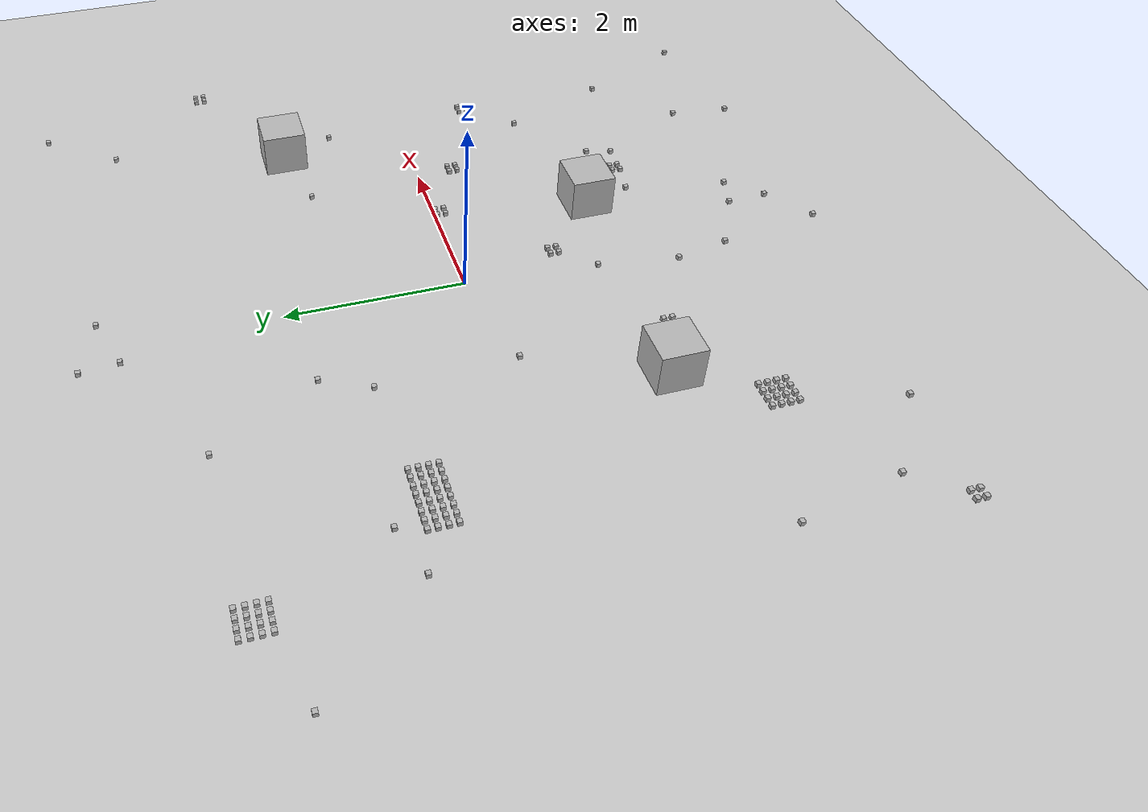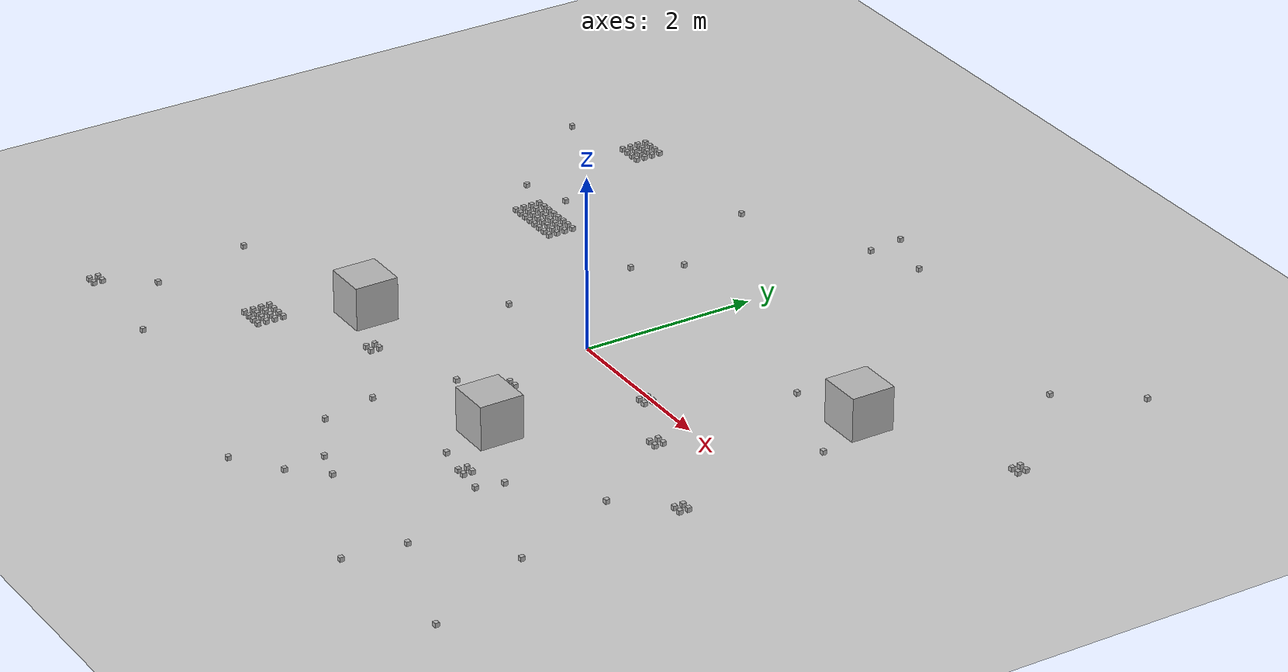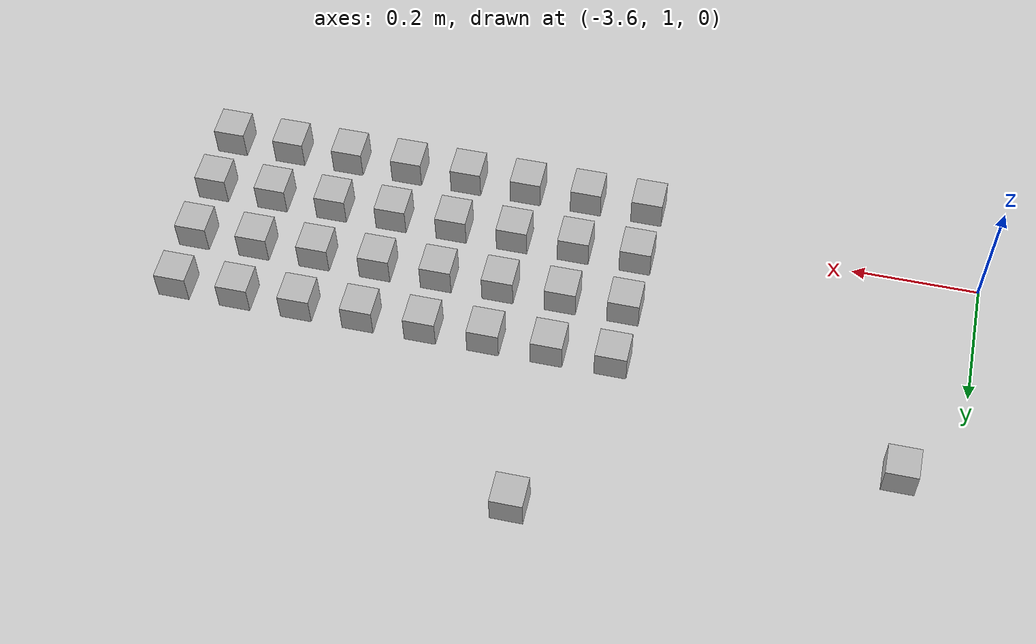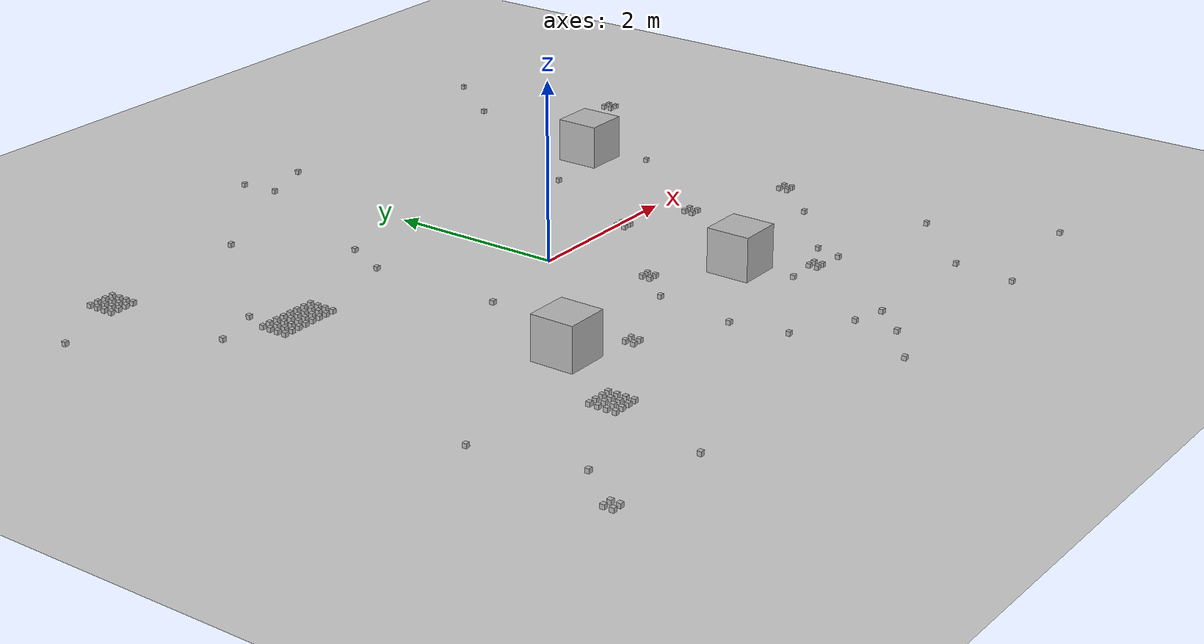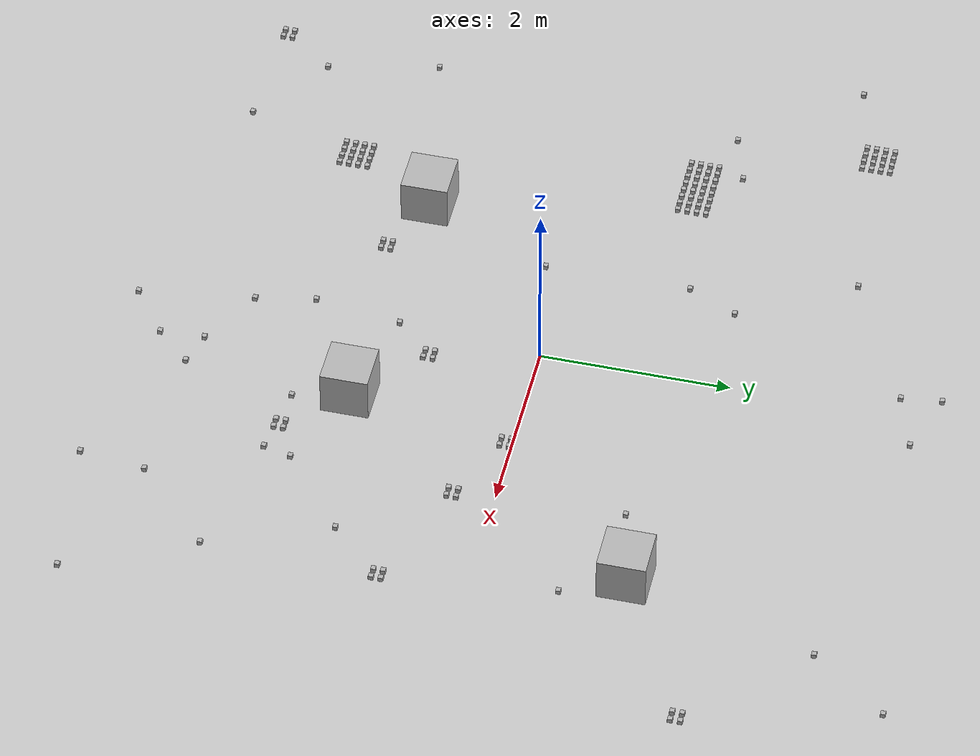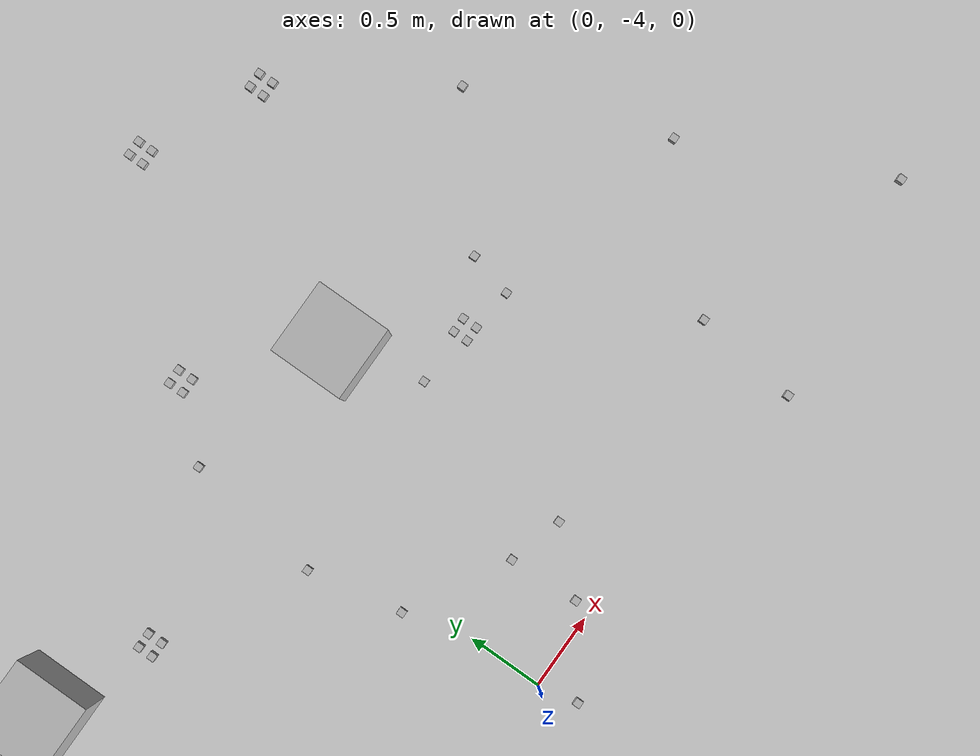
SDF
<sdf version="1.6">
 <world name="default">
  <model name="ground_plane">
   <static>1</static>
   <link name="link">
    <collision name="collision">
     <geometry><plane><normal>0 0 1</normal><size>100 100</size></plane></geometry>
     <surface><friction><ode><mu>100</mu><mu2>50</mu2></ode></friction></surface>
    </collision>
    <visual name="visual">
     <cast_shadows>0</cast_shadows>
     <geometry><plane><normal>0 0 1</normal><size>100 100</size></plane></geometry>
     <material>
      <script><uri>file://media/materials/scripts/gazebo.material</uri><name>Gazebo/Grey</name></script>
     </material>
    </visual>
   </link>
  </model>
  <light name="sun" type="directional">
   <pose>0 0 10 0 -0 0</pose>
   <diffuse>0.8 0.8 0.8 1</diffuse>
   <specular>0.1 0.1 0.1 1</specular>
   <attenuation>
    <range>1000</range>
    <constant>0.9</constant>
    <linear>0.01</linear>
    <quadratic>0.001</quadratic>
   </attenuation>
   <direction>-0.5 0.5 -1</direction>
  </light>
  <plugin name="SetupWorld" filename="libgazebo_plugins.so"/>
  <gravity>0 0 -9.8</gravity>
  <magnetic_field>6e-06 2.3e-05 -4.2e-05</magnetic_field>
  <atmosphere type="adiabatic"/>
  <physics name="default_physics" default="0" type="ode">
   <max_step_size>0.001</max_step_size>
   <real_time_factor>1</real_time_factor>
   <real_time_update_rate>1000</real_time_update_rate>
  </physics>
  <scene><ambient>0.4 0.4 0.4 1</ambient><background>0.7 0.7 0.7 1</background><shadows>1</shadows></scene>
  <spherical_coordinates>
   <surface_model>EARTH_WGS84</surface_model>
   <latitude_deg>0</latitude_deg>
   <longitude_deg>0</longitude_deg>
   <elevation>0</elevation>
   <heading_deg>0</heading_deg>
  </spherical_coordinates>
  <model name="at0">
   <static>0</static>
   <link name="link">
    <inertial>
     <mass>0.01</mass>
     <inertia><ixx>4e-05</ixx><ixy>0</ixy><ixz>0</ixz><iyy>4e-05</iyy><iyz>0</iyz><izz>4e-05</izz></inertia>
    </inertial>
    <visual name="visual">
     <geometry><box><size>0.05 0.05 0.05</size></box></geometry>
     <material>
      <script>
       <uri>model://at0/materials/scripts</uri>
       <uri>model://at0/materials/textures</uri>
       <name>at0/Diffuse</name>
      </script>
     </material>
    </visual>
    <collision name="collision">
     <geometry><box><size>0.05 0.05 0.05</size></box></geometry>
     <surface><friction><ode><mu>0.8</mu><mu2>0.7</mu2></ode></friction></surface>
    </collision>
   </link>
   <pose>-3.06169 0.950554 0.025 0 -0 0</pose>
  </model>
  <model name="at1">
   <static>0</static>
   <link name="link">
    <inertial>
     <mass>0.01</mass>
     <inertia><ixx>4e-05</ixx><ixy>0</ixy><ixz>0</ixz><iyy>4e-05</iyy><iyz>0</iyz><izz>4e-05</izz></inertia>
    </inertial>
    <visual name="visual">
     <geometry><box><size>0.05 0.05 0.05</size></box></geometry>
     <material>
      <script>
       <uri>model://at0/materials/scripts</uri>
       <uri>model://at0/materials/textures</uri>
       <name>at0/Diffuse</name>
      </script>
     </material>
    </visual>
    <collision name="collision">
     <geometry><box><size>0.05 0.05 0.05</size></box></geometry>
     <surface><friction><ode><mu>0.8</mu><mu2>0.7</mu2></ode></friction></surface>
    </collision>
   </link>
   <pose>-2.96169 0.950554 0.025 0 -0 0</pose>
  </model>
  <model name="at2">
   <static>0</static>
   <link name="link">
    <inertial>
     <mass>0.01</mass>
     <inertia><ixx>4e-05</ixx><ixy>0</ixy><ixz>0</ixz><iyy>4e-05</iyy><iyz>0</iyz><izz>4e-05</izz></inertia>
    </inertial>
    <visual name="visual">
     <geometry><box><size>0.05 0.05 0.05</size></box></geometry>
     <material>
      <script>
       <uri>model://at0/materials/scripts</uri>
       <uri>model://at0/materials/textures</uri>
       <name>at0/Diffuse</name>
      </script>
     </material>
    </visual>
    <collision name="collision">
     <geometry><box><size>0.05 0.05 0.05</size></box></geometry>
     <surface><friction><ode><mu>0.8</mu><mu2>0.7</mu2></ode></friction></surface>
    </collision>
   </link>
   <pose>-2.86169 0.950554 0.025 0 -0 0</pose>
  </model>
  <model name="at3">
   <static>0</static>
   <link name="link">
    <inertial>
     <mass>0.01</mass>
     <inertia><ixx>4e-05</ixx><ixy>0</ixy><ixz>0</ixz><iyy>4e-05</iyy><iyz>0</iyz><izz>4e-05</izz></inertia>
    </inertial>
    <visual name="visual">
     <geometry><box><size>0.05 0.05 0.05</size></box></geometry>
     <material>
      <script>
       <uri>model://at0/materials/scripts</uri>
       <uri>model://at0/materials/textures</uri>
       <name>at0/Diffuse</name>
      </script>
     </material>
    </visual>
    <collision name="collision">
     <geometry><box><size>0.05 0.05 0.05</size></box></geometry>
     <surface><friction><ode><mu>0.8</mu><mu2>0.7</mu2></ode></friction></surface>
    </collision>
   </link>
   <pose>-2.76169 0.950554 0.025 0 -0 0</pose>
  </model>
  <model name="at4">
   <static>0</static>
   <link name="link">
    <inertial>
     <mass>0.01</mass>
     <inertia><ixx>4e-05</ixx><ixy>0</ixy><ixz>0</ixz><iyy>4e-05</iyy><iyz>0</iyz><izz>4e-05</izz></inertia>
    </inertial>
    <visual name="visual">
     <geometry><box><size>0.05 0.05 0.05</size></box></geometry>
     <material>
      <script>
       <uri>model://at0/materials/scripts</uri>
       <uri>model://at0/materials/textures</uri>
       <name>at0/Diffuse</name>
      </script>
     </material>
    </visual>
    <collision name="collision">
     <geometry><box><size>0.05 0.05 0.05</size></box></geometry>
     <surface><friction><ode><mu>0.8</mu><mu2>0.7</mu2></ode></friction></surface>
    </collision>
   </link>
   <pose>-2.66169 0.950554 0.025 0 -0 0</pose>
  </model>
  <model name="at5">
   <static>0</static>
   <link name="link">
    <inertial>
     <mass>0.01</mass>
     <inertia><ixx>4e-05</ixx><ixy>0</ixy><ixz>0</ixz><iyy>4e-05</iyy><iyz>0</iyz><izz>4e-05</izz></inertia>
    </inertial>
    <visual name="visual">
     <geometry><box><size>0.05 0.05 0.05</size></box></geometry>
     <material>
      <script>
       <uri>model://at0/materials/scripts</uri>
       <uri>model://at0/materials/textures</uri>
       <name>at0/Diffuse</name>
      </script>
     </material>
    </visual>
    <collision name="collision">
     <geometry><box><size>0.05 0.05 0.05</size></box></geometry>
     <surface><friction><ode><mu>0.8</mu><mu2>0.7</mu2></ode></friction></surface>
    </collision>
   </link>
   <pose>-2.56169 0.950554 0.025 0 -0 0</pose>
  </model>
  <model name="at6">
   <static>0</static>
   <link name="link">
    <inertial>
     <mass>0.01</mass>
     <inertia><ixx>4e-05</ixx><ixy>0</ixy><ixz>0</ixz><iyy>4e-05</iyy><iyz>0</iyz><izz>4e-05</izz></inertia>
    </inertial>
    <visual name="visual">
     <geometry><box><size>0.05 0.05 0.05</size></box></geometry>
     <material>
      <script>
       <uri>model://at0/materials/scripts</uri>
       <uri>model://at0/materials/textures</uri>
       <name>at0/Diffuse</name>
      </script>
     </material>
    </visual>
    <collision name="collision">
     <geometry><box><size>0.05 0.05 0.05</size></box></geometry>
     <surface><friction><ode><mu>0.8</mu><mu2>0.7</mu2></ode></friction></surface>
    </collision>
   </link>
   <pose>-2.46169 0.950554 0.025 0 -0 0</pose>
  </model>
  <model name="at7">
   <static>0</static>
   <link name="link">
    <inertial>
     <mass>0.01</mass>
     <inertia><ixx>4e-05</ixx><ixy>0</ixy><ixz>0</ixz><iyy>4e-05</iyy><iyz>0</iyz><izz>4e-05</izz></inertia>
    </inertial>
    <visual name="visual">
     <geometry><box><size>0.05 0.05 0.05</size></box></geometry>
     <material>
      <script>
       <uri>model://at0/materials/scripts</uri>
       <uri>model://at0/materials/textures</uri>
       <name>at0/Diffuse</name>
      </script>
     </material>
    </visual>
    <collision name="collision">
     <geometry><box><size>0.05 0.05 0.05</size></box></geometry>
     <surface><friction><ode><mu>0.8</mu><mu2>0.7</mu2></ode></friction></surface>
    </collision>
   </link>
   <pose>-2.36169 0.950554 0.025 0 -0 0</pose>
  </model>
  <model name="at8">
   <static>0</static>
   <link name="link">
    <inertial>
     <mass>0.01</mass>
     <inertia><ixx>4e-05</ixx><ixy>0</ixy><ixz>0</ixz><iyy>4e-05</iyy><iyz>0</iyz><izz>4e-05</izz></inertia>
    </inertial>
    <visual name="visual">
     <geometry><box><size>0.05 0.05 0.05</size></box></geometry>
     <material>
      <script>
       <uri>model://at0/materials/scripts</uri>
       <uri>model://at0/materials/textures</uri>
       <name>at0/Diffuse</name>
      </script>
     </material>
    </visual>
    <collision name="collision">
     <geometry><box><size>0.05 0.05 0.05</size></box></geometry>
     <surface><friction><ode><mu>0.8</mu><mu2>0.7</mu2></ode></friction></surface>
    </collision>
   </link>
   <pose>-3.06169 1.05055 0.025 0 -0 0</pose>
  </model>
  <model name="at9">
   <static>0</static>
   <link name="link">
    <inertial>
     <mass>0.01</mass>
     <inertia><ixx>4e-05</ixx><ixy>0</ixy><ixz>0</ixz><iyy>4e-05</iyy><iyz>0</iyz><izz>4e-05</izz></inertia>
    </inertial>
    <visual name="visual">
     <geometry><box><size>0.05 0.05 0.05</size></box></geometry>
     <material>
      <script>
       <uri>model://at0/materials/scripts</uri>
       <uri>model://at0/materials/textures</uri>
       <name>at0/Diffuse</name>
      </script>
     </material>
    </visual>
    <collision name="collision">
     <geometry><box><size>0.05 0.05 0.05</size></box></geometry>
     <surface><friction><ode><mu>0.8</mu><mu2>0.7</mu2></ode></friction></surface>
    </collision>
   </link>
   <pose>-2.96169 1.05055 0.025 0 -0 0</pose>
  </model>
  <model name="at10">
   <static>0</static>
   <link name="link">
    <inertial>
     <mass>0.01</mass>
     <inertia><ixx>4e-05</ixx><ixy>0</ixy><ixz>0</ixz><iyy>4e-05</iyy><iyz>0</iyz><izz>4e-05</izz></inertia>
    </inertial>
    <visual name="visual">
     <geometry><box><size>0.05 0.05 0.05</size></box></geometry>
     <material>
      <script>
       <uri>model://at0/materials/scripts</uri>
       <uri>model://at0/materials/textures</uri>
       <name>at0/Diffuse</name>
      </script>
     </material>
    </visual>
    <collision name="collision">
     <geometry><box><size>0.05 0.05 0.05</size></box></geometry>
     <surface><friction><ode><mu>0.8</mu><mu2>0.7</mu2></ode></friction></surface>
    </collision>
   </link>
   <pose>-2.86169 1.05055 0.025 0 -0 0</pose>
  </model>
  <model name="at11">
   <static>0</static>
   <link name="link">
    <inertial>
     <mass>0.01</mass>
     <inertia><ixx>4e-05</ixx><ixy>0</ixy><ixz>0</ixz><iyy>4e-05</iyy><iyz>0</iyz><izz>4e-05</izz></inertia>
    </inertial>
    <visual name="visual">
     <geometry><box><size>0.05 0.05 0.05</size></box></geometry>
     <material>
      <script>
       <uri>model://at0/materials/scripts</uri>
       <uri>model://at0/materials/textures</uri>
       <name>at0/Diffuse</name>
      </script>
     </material>
    </visual>
    <collision name="collision">
     <geometry><box><size>0.05 0.05 0.05</size></box></geometry>
     <surface><friction><ode><mu>0.8</mu><mu2>0.7</mu2></ode></friction></surface>
    </collision>
   </link>
   <pose>-2.76169 1.05055 0.025 0 -0 0</pose>
  </model>
  <model name="at12">
   <static>0</static>
   <link name="link">
    <inertial>
     <mass>0.01</mass>
     <inertia><ixx>4e-05</ixx><ixy>0</ixy><ixz>0</ixz><iyy>4e-05</iyy><iyz>0</iyz><izz>4e-05</izz></inertia>
    </inertial>
    <visual name="visual">
     <geometry><box><size>0.05 0.05 0.05</size></box></geometry>
     <material>
      <script>
       <uri>model://at0/materials/scripts</uri>
       <uri>model://at0/materials/textures</uri>
       <name>at0/Diffuse</name>
      </script>
     </material>
    </visual>
    <collision name="collision">
     <geometry><box><size>0.05 0.05 0.05</size></box></geometry>
     <surface><friction><ode><mu>0.8</mu><mu2>0.7</mu2></ode></friction></surface>
    </collision>
   </link>
   <pose>-2.66169 1.05055 0.025 0 -0 0</pose>
  </model>
  <model name="at13">
   <static>0</static>
   <link name="link">
    <inertial>
     <mass>0.01</mass>
     <inertia><ixx>4e-05</ixx><ixy>0</ixy><ixz>0</ixz><iyy>4e-05</iyy><iyz>0</iyz><izz>4e-05</izz></inertia>
    </inertial>
    <visual name="visual">
     <geometry><box><size>0.05 0.05 0.05</size></box></geometry>
     <material>
      <script>
       <uri>model://at0/materials/scripts</uri>
       <uri>model://at0/materials/textures</uri>
       <name>at0/Diffuse</name>
      </script>
     </material>
    </visual>
    <collision name="collision">
     <geometry><box><size>0.05 0.05 0.05</size></box></geometry>
     <surface><friction><ode><mu>0.8</mu><mu2>0.7</mu2></ode></friction></surface>
    </collision>
   </link>
   <pose>-2.56169 1.05055 0.025 0 -0 0</pose>
  </model>
  <model name="at14">
   <static>0</static>
   <link name="link">
    <inertial>
     <mass>0.01</mass>
     <inertia><ixx>4e-05</ixx><ixy>0</ixy><ixz>0</ixz><iyy>4e-05</iyy><iyz>0</iyz><izz>4e-05</izz></inertia>
    </inertial>
    <visual name="visual">
     <geometry><box><size>0.05 0.05 0.05</size></box></geometry>
     <material>
      <script>
       <uri>model://at0/materials/scripts</uri>
       <uri>model://at0/materials/textures</uri>
       <name>at0/Diffuse</name>
      </script>
     </material>
    </visual>
    <collision name="collision">
     <geometry><box><size>0.05 0.05 0.05</size></box></geometry>
     <surface><friction><ode><mu>0.8</mu><mu2>0.7</mu2></ode></friction></surface>
    </collision>
   </link>
   <pose>-2.46169 1.05055 0.025 0 -0 0</pose>
  </model>
  <model name="at15">
   <static>0</static>
   <link name="link">
    <inertial>
     <mass>0.01</mass>
     <inertia><ixx>4e-05</ixx><ixy>0</ixy><ixz>0</ixz><iyy>4e-05</iyy><iyz>0</iyz><izz>4e-05</izz></inertia>
    </inertial>
    <visual name="visual">
     <geometry><box><size>0.05 0.05 0.05</size></box></geometry>
     <material>
      <script>
       <uri>model://at0/materials/scripts</uri>
       <uri>model://at0/materials/textures</uri>
       <name>at0/Diffuse</name>
      </script>
     </material>
    </visual>
    <collision name="collision">
     <geometry><box><size>0.05 0.05 0.05</size></box></geometry>
     <surface><friction><ode><mu>0.8</mu><mu2>0.7</mu2></ode></friction></surface>
    </collision>
   </link>
   <pose>-2.36169 1.05055 0.025 0 -0 0</pose>
  </model>
  <model name="at16">
   <static>0</static>
   <link name="link">
    <inertial>
     <mass>0.01</mass>
     <inertia><ixx>4e-05</ixx><ixy>0</ixy><ixz>0</ixz><iyy>4e-05</iyy><iyz>0</iyz><izz>4e-05</izz></inertia>
    </inertial>
    <visual name="visual">
     <geometry><box><size>0.05 0.05 0.05</size></box></geometry>
     <material>
      <script>
       <uri>model://at0/materials/scripts</uri>
       <uri>model://at0/materials/textures</uri>
       <name>at0/Diffuse</name>
      </script>
     </material>
    </visual>
    <collision name="collision">
     <geometry><box><size>0.05 0.05 0.05</size></box></geometry>
     <surface><friction><ode><mu>0.8</mu><mu2>0.7</mu2></ode></friction></surface>
    </collision>
   </link>
   <pose>-3.06169 1.15055 0.025 0 -0 0</pose>
  </model>
  <model name="at17">
   <static>0</static>
   <link name="link">
    <inertial>
     <mass>0.01</mass>
     <inertia><ixx>4e-05</ixx><ixy>0</ixy><ixz>0</ixz><iyy>4e-05</iyy><iyz>0</iyz><izz>4e-05</izz></inertia>
    </inertial>
    <visual name="visual">
     <geometry><box><size>0.05 0.05 0.05</size></box></geometry>
     <material>
      <script>
       <uri>model://at0/materials/scripts</uri>
       <uri>model://at0/materials/textures</uri>
       <name>at0/Diffuse</name>
      </script>
     </material>
    </visual>
    <collision name="collision">
     <geometry><box><size>0.05 0.05 0.05</size></box></geometry>
     <surface><friction><ode><mu>0.8</mu><mu2>0.7</mu2></ode></friction></surface>
    </collision>
   </link>
   <pose>-2.96169 1.15055 0.025 0 -0 0</pose>
  </model>
  <model name="at18">
   <static>0</static>
   <link name="link">
    <inertial>
     <mass>0.01</mass>
     <inertia><ixx>4e-05</ixx><ixy>0</ixy><ixz>0</ixz><iyy>4e-05</iyy><iyz>0</iyz><izz>4e-05</izz></inertia>
    </inertial>
    <visual name="visual">
     <geometry><box><size>0.05 0.05 0.05</size></box></geometry>
     <material>
      <script>
       <uri>model://at0/materials/scripts</uri>
       <uri>model://at0/materials/textures</uri>
       <name>at0/Diffuse</name>
      </script>
     </material>
    </visual>
    <collision name="collision">
     <geometry><box><size>0.05 0.05 0.05</size></box></geometry>
     <surface><friction><ode><mu>0.8</mu><mu2>0.7</mu2></ode></friction></surface>
    </collision>
   </link>
   <pose>-2.86169 1.15055 0.025 0 -0 0</pose>
  </model>
  <model name="at19">
   <static>0</static>
   <link name="link">
    <inertial>
     <mass>0.01</mass>
     <inertia><ixx>4e-05</ixx><ixy>0</ixy><ixz>0</ixz><iyy>4e-05</iyy><iyz>0</iyz><izz>4e-05</izz></inertia>
    </inertial>
    <visual name="visual">
     <geometry><box><size>0.05 0.05 0.05</size></box></geometry>
     <material>
      <script>
       <uri>model://at0/materials/scripts</uri>
       <uri>model://at0/materials/textures</uri>
       <name>at0/Diffuse</name>
      </script>
     </material>
    </visual>
    <collision name="collision">
     <geometry><box><size>0.05 0.05 0.05</size></box></geometry>
     <surface><friction><ode><mu>0.8</mu><mu2>0.7</mu2></ode></friction></surface>
    </collision>
   </link>
   <pose>-2.76169 1.15055 0.025 0 -0 0</pose>
  </model>
  <model name="at20">
   <static>0</static>
   <link name="link">
    <inertial>
     <mass>0.01</mass>
     <inertia><ixx>4e-05</ixx><ixy>0</ixy><ixz>0</ixz><iyy>4e-05</iyy><iyz>0</iyz><izz>4e-05</izz></inertia>
    </inertial>
    <visual name="visual">
     <geometry><box><size>0.05 0.05 0.05</size></box></geometry>
     <material>
      <script>
       <uri>model://at0/materials/scripts</uri>
       <uri>model://at0/materials/textures</uri>
       <name>at0/Diffuse</name>
      </script>
     </material>
    </visual>
    <collision name="collision">
     <geometry><box><size>0.05 0.05 0.05</size></box></geometry>
     <surface><friction><ode><mu>0.8</mu><mu2>0.7</mu2></ode></friction></surface>
    </collision>
   </link>
   <pose>-2.66169 1.15055 0.025 0 -0 0</pose>
  </model>
  <model name="at21">
   <static>0</static>
   <link name="link">
    <inertial>
     <mass>0.01</mass>
     <inertia><ixx>4e-05</ixx><ixy>0</ixy><ixz>0</ixz><iyy>4e-05</iyy><iyz>0</iyz><izz>4e-05</izz></inertia>
    </inertial>
    <visual name="visual">
     <geometry><box><size>0.05 0.05 0.05</size></box></geometry>
     <material>
      <script>
       <uri>model://at0/materials/scripts</uri>
       <uri>model://at0/materials/textures</uri>
       <name>at0/Diffuse</name>
      </script>
     </material>
    </visual>
    <collision name="collision">
     <geometry><box><size>0.05 0.05 0.05</size></box></geometry>
     <surface><friction><ode><mu>0.8</mu><mu2>0.7</mu2></ode></friction></surface>
    </collision>
   </link>
   <pose>-2.56169 1.15055 0.025 0 -0 0</pose>
  </model>
  <model name="at22">
   <static>0</static>
   <link name="link">
    <inertial>
     <mass>0.01</mass>
     <inertia><ixx>4e-05</ixx><ixy>0</ixy><ixz>0</ixz><iyy>4e-05</iyy><iyz>0</iyz><izz>4e-05</izz></inertia>
    </inertial>
    <visual name="visual">
     <geometry><box><size>0.05 0.05 0.05</size></box></geometry>
     <material>
      <script>
       <uri>model://at0/materials/scripts</uri>
       <uri>model://at0/materials/textures</uri>
       <name>at0/Diffuse</name>
      </script>
     </material>
    </visual>
    <collision name="collision">
     <geometry><box><size>0.05 0.05 0.05</size></box></geometry>
     <surface><friction><ode><mu>0.8</mu><mu2>0.7</mu2></ode></friction></surface>
    </collision>
   </link>
   <pose>-2.46169 1.15055 0.025 0 -0 0</pose>
  </model>
  <model name="at23">
   <static>0</static>
   <link name="link">
    <inertial>
     <mass>0.01</mass>
     <inertia><ixx>4e-05</ixx><ixy>0</ixy><ixz>0</ixz><iyy>4e-05</iyy><iyz>0</iyz><izz>4e-05</izz></inertia>
    </inertial>
    <visual name="visual">
     <geometry><box><size>0.05 0.05 0.05</size></box></geometry>
     <material>
      <script>
       <uri>model://at0/materials/scripts</uri>
       <uri>model://at0/materials/textures</uri>
       <name>at0/Diffuse</name>
      </script>
     </material>
    </visual>
    <collision name="collision">
     <geometry><box><size>0.05 0.05 0.05</size></box></geometry>
     <surface><friction><ode><mu>0.8</mu><mu2>0.7</mu2></ode></friction></surface>
    </collision>
   </link>
   <pose>-2.36169 1.15055 0.025 0 -0 0</pose>
  </model>
  <model name="at24">
   <static>0</static>
   <link name="link">
    <inertial>
     <mass>0.01</mass>
     <inertia><ixx>4e-05</ixx><ixy>0</ixy><ixz>0</ixz><iyy>4e-05</iyy><iyz>0</iyz><izz>4e-05</izz></inertia>
    </inertial>
    <visual name="visual">
     <geometry><box><size>0.05 0.05 0.05</size></box></geometry>
     <material>
      <script>
       <uri>model://at0/materials/scripts</uri>
       <uri>model://at0/materials/textures</uri>
       <name>at0/Diffuse</name>
      </script>
     </material>
    </visual>
    <collision name="collision">
     <geometry><box><size>0.05 0.05 0.05</size></box></geometry>
     <surface><friction><ode><mu>0.8</mu><mu2>0.7</mu2></ode></friction></surface>
    </collision>
   </link>
   <pose>-3.06169 1.25055 0.025 0 -0 0</pose>
  </model>
  <model name="at25">
   <static>0</static>
   <link name="link">
    <inertial>
     <mass>0.01</mass>
     <inertia><ixx>4e-05</ixx><ixy>0</ixy><ixz>0</ixz><iyy>4e-05</iyy><iyz>0</iyz><izz>4e-05</izz></inertia>
    </inertial>
    <visual name="visual">
     <geometry><box><size>0.05 0.05 0.05</size></box></geometry>
     <material>
      <script>
       <uri>model://at0/materials/scripts</uri>
       <uri>model://at0/materials/textures</uri>
       <name>at0/Diffuse</name>
      </script>
     </material>
    </visual>
    <collision name="collision">
     <geometry><box><size>0.05 0.05 0.05</size></box></geometry>
     <surface><friction><ode><mu>0.8</mu><mu2>0.7</mu2></ode></friction></surface>
    </collision>
   </link>
   <pose>-2.96169 1.25055 0.025 0 -0 0</pose>
  </model>
  <model name="at26">
   <static>0</static>
   <link name="link">
    <inertial>
     <mass>0.01</mass>
     <inertia><ixx>4e-05</ixx><ixy>0</ixy><ixz>0</ixz><iyy>4e-05</iyy><iyz>0</iyz><izz>4e-05</izz></inertia>
    </inertial>
    <visual name="visual">
     <geometry><box><size>0.05 0.05 0.05</size></box></geometry>
     <material>
      <script>
       <uri>model://at0/materials/scripts</uri>
       <uri>model://at0/materials/textures</uri>
       <name>at0/Diffuse</name>
      </script>
     </material>
    </visual>
    <collision name="collision">
     <geometry><box><size>0.05 0.05 0.05</size></box></geometry>
     <surface><friction><ode><mu>0.8</mu><mu2>0.7</mu2></ode></friction></surface>
    </collision>
   </link>
   <pose>-2.86169 1.25055 0.025 0 -0 0</pose>
  </model>
  <model name="at27">
   <static>0</static>
   <link name="link">
    <inertial>
     <mass>0.01</mass>
     <inertia><ixx>4e-05</ixx><ixy>0</ixy><ixz>0</ixz><iyy>4e-05</iyy><iyz>0</iyz><izz>4e-05</izz></inertia>
    </inertial>
    <visual name="visual">
     <geometry><box><size>0.05 0.05 0.05</size></box></geometry>
     <material>
      <script>
       <uri>model://at0/materials/scripts</uri>
       <uri>model://at0/materials/textures</uri>
       <name>at0/Diffuse</name>
      </script>
     </material>
    </visual>
    <collision name="collision">
     <geometry><box><size>0.05 0.05 0.05</size></box></geometry>
     <surface><friction><ode><mu>0.8</mu><mu2>0.7</mu2></ode></friction></surface>
    </collision>
   </link>
   <pose>-2.76169 1.25055 0.025 0 -0 0</pose>
  </model>
  <model name="at28">
   <static>0</static>
   <link name="link">
    <inertial>
     <mass>0.01</mass>
     <inertia><ixx>4e-05</ixx><ixy>0</ixy><ixz>0</ixz><iyy>4e-05</iyy><iyz>0</iyz><izz>4e-05</izz></inertia>
    </inertial>
    <visual name="visual">
     <geometry><box><size>0.05 0.05 0.05</size></box></geometry>
     <material>
      <script>
       <uri>model://at0/materials/scripts</uri>
       <uri>model://at0/materials/textures</uri>
       <name>at0/Diffuse</name>
      </script>
     </material>
    </visual>
    <collision name="collision">
     <geometry><box><size>0.05 0.05 0.05</size></box></geometry>
     <surface><friction><ode><mu>0.8</mu><mu2>0.7</mu2></ode></friction></surface>
    </collision>
   </link>
   <pose>-2.66169 1.25055 0.025 0 -0 0</pose>
  </model>
  <model name="at29">
   <static>0</static>
   <link name="link">
    <inertial>
     <mass>0.01</mass>
     <inertia><ixx>4e-05</ixx><ixy>0</ixy><ixz>0</ixz><iyy>4e-05</iyy><iyz>0</iyz><izz>4e-05</izz></inertia>
    </inertial>
    <visual name="visual">
     <geometry><box><size>0.05 0.05 0.05</size></box></geometry>
     <material>
      <script>
       <uri>model://at0/materials/scripts</uri>
       <uri>model://at0/materials/textures</uri>
       <name>at0/Diffuse</name>
      </script>
     </material>
    </visual>
    <collision name="collision">
     <geometry><box><size>0.05 0.05 0.05</size></box></geometry>
     <surface><friction><ode><mu>0.8</mu><mu2>0.7</mu2></ode></friction></surface>
    </collision>
   </link>
   <pose>-2.56169 1.25055 0.025 0 -0 0</pose>
  </model>
  <model name="at30">
   <static>0</static>
   <link name="link">
    <inertial>
     <mass>0.01</mass>
     <inertia><ixx>4e-05</ixx><ixy>0</ixy><ixz>0</ixz><iyy>4e-05</iyy><iyz>0</iyz><izz>4e-05</izz></inertia>
    </inertial>
    <visual name="visual">
     <geometry><box><size>0.05 0.05 0.05</size></box></geometry>
     <material>
      <script>
       <uri>model://at0/materials/scripts</uri>
       <uri>model://at0/materials/textures</uri>
       <name>at0/Diffuse</name>
      </script>
     </material>
    </visual>
    <collision name="collision">
     <geometry><box><size>0.05 0.05 0.05</size></box></geometry>
     <surface><friction><ode><mu>0.8</mu><mu2>0.7</mu2></ode></friction></surface>
    </collision>
   </link>
   <pose>-2.46169 1.25055 0.025 0 -0 0</pose>
  </model>
  <model name="at31">
   <static>0</static>
   <link name="link">
    <inertial>
     <mass>0.01</mass>
     <inertia><ixx>4e-05</ixx><ixy>0</ixy><ixz>0</ixz><iyy>4e-05</iyy><iyz>0</iyz><izz>4e-05</izz></inertia>
    </inertial>
    <visual name="visual">
     <geometry><box><size>0.05 0.05 0.05</size></box></geometry>
     <material>
      <script>
       <uri>model://at0/materials/scripts</uri>
       <uri>model://at0/materials/textures</uri>
       <name>at0/Diffuse</name>
      </script>
     </material>
    </visual>
    <collision name="collision">
     <geometry><box><size>0.05 0.05 0.05</size></box></geometry>
     <surface><friction><ode><mu>0.8</mu><mu2>0.7</mu2></ode></friction></surface>
    </collision>
   </link>
   <pose>-2.36169 1.25055 0.025 0 -0 0</pose>
  </model>
  <model name="at32">
   <static>0</static>
   <link name="link">
    <inertial>
     <mass>0.01</mass>
     <inertia><ixx>4e-05</ixx><ixy>0</ixy><ixz>0</ixz><iyy>4e-05</iyy><iyz>0</iyz><izz>4e-05</izz></inertia>
    </inertial>
    <visual name="visual">
     <geometry><box><size>0.05 0.05 0.05</size></box></geometry>
     <material>
      <script>
       <uri>model://at0/materials/scripts</uri>
       <uri>model://at0/materials/textures</uri>
       <name>at0/Diffuse</name>
      </script>
     </material>
    </visual>
    <collision name="collision">
     <geometry><box><size>0.05 0.05 0.05</size></box></geometry>
     <surface><friction><ode><mu>0.8</mu><mu2>0.7</mu2></ode></friction></surface>
    </collision>
   </link>
   <pose>-2.54789 -2.68596 0.025 0 -0 0</pose>
  </model>
  <model name="at33">
   <static>0</static>
   <link name="link">
    <inertial>
     <mass>0.01</mass>
     <inertia><ixx>4e-05</ixx><ixy>0</ixy><ixz>0</ixz><iyy>4e-05</iyy><iyz>0</iyz><izz>4e-05</izz></inertia>
    </inertial>
    <visual name="visual">
     <geometry><box><size>0.05 0.05 0.05</size></box></geometry>
     <material>
      <script>
       <uri>model://at0/materials/scripts</uri>
       <uri>model://at0/materials/textures</uri>
       <name>at0/Diffuse</name>
      </script>
     </material>
    </visual>
    <collision name="collision">
     <geometry><box><size>0.05 0.05 0.05</size></box></geometry>
     <surface><friction><ode><mu>0.8</mu><mu2>0.7</mu2></ode></friction></surface>
    </collision>
   </link>
   <pose>-2.44789 -2.68596 0.025 0 -0 0</pose>
  </model>
  <model name="at34">
   <static>0</static>
   <link name="link">
    <inertial>
     <mass>0.01</mass>
     <inertia><ixx>4e-05</ixx><ixy>0</ixy><ixz>0</ixz><iyy>4e-05</iyy><iyz>0</iyz><izz>4e-05</izz></inertia>
    </inertial>
    <visual name="visual">
     <geometry><box><size>0.05 0.05 0.05</size></box></geometry>
     <material>
      <script>
       <uri>model://at0/materials/scripts</uri>
       <uri>model://at0/materials/textures</uri>
       <name>at0/Diffuse</name>
      </script>
     </material>
    </visual>
    <collision name="collision">
     <geometry><box><size>0.05 0.05 0.05</size></box></geometry>
     <surface><friction><ode><mu>0.8</mu><mu2>0.7</mu2></ode></friction></surface>
    </collision>
   </link>
   <pose>-2.34789 -2.68596 0.025 0 -0 0</pose>
  </model>
  <model name="at35">
   <static>0</static>
   <link name="link">
    <inertial>
     <mass>0.01</mass>
     <inertia><ixx>4e-05</ixx><ixy>0</ixy><ixz>0</ixz><iyy>4e-05</iyy><iyz>0</iyz><izz>4e-05</izz></inertia>
    </inertial>
    <visual name="visual">
     <geometry><box><size>0.05 0.05 0.05</size></box></geometry>
     <material>
      <script>
       <uri>model://at0/materials/scripts</uri>
       <uri>model://at0/materials/textures</uri>
       <name>at0/Diffuse</name>
      </script>
     </material>
    </visual>
    <collision name="collision">
     <geometry><box><size>0.05 0.05 0.05</size></box></geometry>
     <surface><friction><ode><mu>0.8</mu><mu2>0.7</mu2></ode></friction></surface>
    </collision>
   </link>
   <pose>-2.24789 -2.68596 0.025 0 -0 0</pose>
  </model>
  <model name="at36">
   <static>0</static>
   <link name="link">
    <inertial>
     <mass>0.01</mass>
     <inertia><ixx>4e-05</ixx><ixy>0</ixy><ixz>0</ixz><iyy>4e-05</iyy><iyz>0</iyz><izz>4e-05</izz></inertia>
    </inertial>
    <visual name="visual">
     <geometry><box><size>0.05 0.05 0.05</size></box></geometry>
     <material>
      <script>
       <uri>model://at0/materials/scripts</uri>
       <uri>model://at0/materials/textures</uri>
       <name>at0/Diffuse</name>
      </script>
     </material>
    </visual>
    <collision name="collision">
     <geometry><box><size>0.05 0.05 0.05</size></box></geometry>
     <surface><friction><ode><mu>0.8</mu><mu2>0.7</mu2></ode></friction></surface>
    </collision>
   </link>
   <pose>-2.54789 -2.58596 0.025 0 -0 0</pose>
  </model>
  <model name="at37">
   <static>0</static>
   <link name="link">
    <inertial>
     <mass>0.01</mass>
     <inertia><ixx>4e-05</ixx><ixy>0</ixy><ixz>0</ixz><iyy>4e-05</iyy><iyz>0</iyz><izz>4e-05</izz></inertia>
    </inertial>
    <visual name="visual">
     <geometry><box><size>0.05 0.05 0.05</size></box></geometry>
     <material>
      <script>
       <uri>model://at0/materials/scripts</uri>
       <uri>model://at0/materials/textures</uri>
       <name>at0/Diffuse</name>
      </script>
     </material>
    </visual>
    <collision name="collision">
     <geometry><box><size>0.05 0.05 0.05</size></box></geometry>
     <surface><friction><ode><mu>0.8</mu><mu2>0.7</mu2></ode></friction></surface>
    </collision>
   </link>
   <pose>-2.44789 -2.58596 0.025 0 -0 0</pose>
  </model>
  <model name="at38">
   <static>0</static>
   <link name="link">
    <inertial>
     <mass>0.01</mass>
     <inertia><ixx>4e-05</ixx><ixy>0</ixy><ixz>0</ixz><iyy>4e-05</iyy><iyz>0</iyz><izz>4e-05</izz></inertia>
    </inertial>
    <visual name="visual">
     <geometry><box><size>0.05 0.05 0.05</size></box></geometry>
     <material>
      <script>
       <uri>model://at0/materials/scripts</uri>
       <uri>model://at0/materials/textures</uri>
       <name>at0/Diffuse</name>
      </script>
     </material>
    </visual>
    <collision name="collision">
     <geometry><box><size>0.05 0.05 0.05</size></box></geometry>
     <surface><friction><ode><mu>0.8</mu><mu2>0.7</mu2></ode></friction></surface>
    </collision>
   </link>
   <pose>-2.34789 -2.58596 0.025 0 -0 0</pose>
  </model>
  <model name="at39">
   <static>0</static>
   <link name="link">
    <inertial>
     <mass>0.01</mass>
     <inertia><ixx>4e-05</ixx><ixy>0</ixy><ixz>0</ixz><iyy>4e-05</iyy><iyz>0</iyz><izz>4e-05</izz></inertia>
    </inertial>
    <visual name="visual">
     <geometry><box><size>0.05 0.05 0.05</size></box></geometry>
     <material>
      <script>
       <uri>model://at0/materials/scripts</uri>
       <uri>model://at0/materials/textures</uri>
       <name>at0/Diffuse</name>
      </script>
     </material>
    </visual>
    <collision name="collision">
     <geometry><box><size>0.05 0.05 0.05</size></box></geometry>
     <surface><friction><ode><mu>0.8</mu><mu2>0.7</mu2></ode></friction></surface>
    </collision>
   </link>
   <pose>-2.24789 -2.58596 0.025 0 -0 0</pose>
  </model>
  <model name="at40">
   <static>0</static>
   <link name="link">
    <inertial>
     <mass>0.01</mass>
     <inertia><ixx>4e-05</ixx><ixy>0</ixy><ixz>0</ixz><iyy>4e-05</iyy><iyz>0</iyz><izz>4e-05</izz></inertia>
    </inertial>
    <visual name="visual">
     <geometry><box><size>0.05 0.05 0.05</size></box></geometry>
     <material>
      <script>
       <uri>model://at0/materials/scripts</uri>
       <uri>model://at0/materials/textures</uri>
       <name>at0/Diffuse</name>
      </script>
     </material>
    </visual>
    <collision name="collision">
     <geometry><box><size>0.05 0.05 0.05</size></box></geometry>
     <surface><friction><ode><mu>0.8</mu><mu2>0.7</mu2></ode></friction></surface>
    </collision>
   </link>
   <pose>-2.54789 -2.48596 0.025 0 -0 0</pose>
  </model>
  <model name="at41">
   <static>0</static>
   <link name="link">
    <inertial>
     <mass>0.01</mass>
     <inertia><ixx>4e-05</ixx><ixy>0</ixy><ixz>0</ixz><iyy>4e-05</iyy><iyz>0</iyz><izz>4e-05</izz></inertia>
    </inertial>
    <visual name="visual">
     <geometry><box><size>0.05 0.05 0.05</size></box></geometry>
     <material>
      <script>
       <uri>model://at0/materials/scripts</uri>
       <uri>model://at0/materials/textures</uri>
       <name>at0/Diffuse</name>
      </script>
     </material>
    </visual>
    <collision name="collision">
     <geometry><box><size>0.05 0.05 0.05</size></box></geometry>
     <surface><friction><ode><mu>0.8</mu><mu2>0.7</mu2></ode></friction></surface>
    </collision>
   </link>
   <pose>-2.44789 -2.48596 0.025 0 -0 0</pose>
  </model>
  <model name="at42">
   <static>0</static>
   <link name="link">
    <inertial>
     <mass>0.01</mass>
     <inertia><ixx>4e-05</ixx><ixy>0</ixy><ixz>0</ixz><iyy>4e-05</iyy><iyz>0</iyz><izz>4e-05</izz></inertia>
    </inertial>
    <visual name="visual">
     <geometry><box><size>0.05 0.05 0.05</size></box></geometry>
     <material>
      <script>
       <uri>model://at0/materials/scripts</uri>
       <uri>model://at0/materials/textures</uri>
       <name>at0/Diffuse</name>
      </script>
     </material>
    </visual>
    <collision name="collision">
     <geometry><box><size>0.05 0.05 0.05</size></box></geometry>
     <surface><friction><ode><mu>0.8</mu><mu2>0.7</mu2></ode></friction></surface>
    </collision>
   </link>
   <pose>-2.34789 -2.48596 0.025 0 -0 0</pose>
  </model>
  <model name="at43">
   <static>0</static>
   <link name="link">
    <inertial>
     <mass>0.01</mass>
     <inertia><ixx>4e-05</ixx><ixy>0</ixy><ixz>0</ixz><iyy>4e-05</iyy><iyz>0</iyz><izz>4e-05</izz></inertia>
    </inertial>
    <visual name="visual">
     <geometry><box><size>0.05 0.05 0.05</size></box></geometry>
     <material>
      <script>
       <uri>model://at0/materials/scripts</uri>
       <uri>model://at0/materials/textures</uri>
       <name>at0/Diffuse</name>
      </script>
     </material>
    </visual>
    <collision name="collision">
     <geometry><box><size>0.05 0.05 0.05</size></box></geometry>
     <surface><friction><ode><mu>0.8</mu><mu2>0.7</mu2></ode></friction></surface>
    </collision>
   </link>
   <pose>-2.24789 -2.48596 0.025 0 -0 0</pose>
  </model>
  <model name="at44">
   <static>0</static>
   <link name="link">
    <inertial>
     <mass>0.01</mass>
     <inertia><ixx>4e-05</ixx><ixy>0</ixy><ixz>0</ixz><iyy>4e-05</iyy><iyz>0</iyz><izz>4e-05</izz></inertia>
    </inertial>
    <visual name="visual">
     <geometry><box><size>0.05 0.05 0.05</size></box></geometry>
     <material>
      <script>
       <uri>model://at0/materials/scripts</uri>
       <uri>model://at0/materials/textures</uri>
       <name>at0/Diffuse</name>
      </script>
     </material>
    </visual>
    <collision name="collision">
     <geometry><box><size>0.05 0.05 0.05</size></box></geometry>
     <surface><friction><ode><mu>0.8</mu><mu2>0.7</mu2></ode></friction></surface>
    </collision>
   </link>
   <pose>-2.54789 -2.38596 0.025 0 -0 0</pose>
  </model>
  <model name="at45">
   <static>0</static>
   <link name="link">
    <inertial>
     <mass>0.01</mass>
     <inertia><ixx>4e-05</ixx><ixy>0</ixy><ixz>0</ixz><iyy>4e-05</iyy><iyz>0</iyz><izz>4e-05</izz></inertia>
    </inertial>
    <visual name="visual">
     <geometry><box><size>0.05 0.05 0.05</size></box></geometry>
     <material>
      <script>
       <uri>model://at0/materials/scripts</uri>
       <uri>model://at0/materials/textures</uri>
       <name>at0/Diffuse</name>
      </script>
     </material>
    </visual>
    <collision name="collision">
     <geometry><box><size>0.05 0.05 0.05</size></box></geometry>
     <surface><friction><ode><mu>0.8</mu><mu2>0.7</mu2></ode></friction></surface>
    </collision>
   </link>
   <pose>-2.44789 -2.38596 0.025 0 -0 0</pose>
  </model>
  <model name="at46">
   <static>0</static>
   <link name="link">
    <inertial>
     <mass>0.01</mass>
     <inertia><ixx>4e-05</ixx><ixy>0</ixy><ixz>0</ixz><iyy>4e-05</iyy><iyz>0</iyz><izz>4e-05</izz></inertia>
    </inertial>
    <visual name="visual">
     <geometry><box><size>0.05 0.05 0.05</size></box></geometry>
     <material>
      <script>
       <uri>model://at0/materials/scripts</uri>
       <uri>model://at0/materials/textures</uri>
       <name>at0/Diffuse</name>
      </script>
     </material>
    </visual>
    <collision name="collision">
     <geometry><box><size>0.05 0.05 0.05</size></box></geometry>
     <surface><friction><ode><mu>0.8</mu><mu2>0.7</mu2></ode></friction></surface>
    </collision>
   </link>
   <pose>-2.34789 -2.38596 0.025 0 -0 0</pose>
  </model>
  <model name="at47">
   <static>0</static>
   <link name="link">
    <inertial>
     <mass>0.01</mass>
     <inertia><ixx>4e-05</ixx><ixy>0</ixy><ixz>0</ixz><iyy>4e-05</iyy><iyz>0</iyz><izz>4e-05</izz></inertia>
    </inertial>
    <visual name="visual">
     <geometry><box><size>0.05 0.05 0.05</size></box></geometry>
     <material>
      <script>
       <uri>model://at0/materials/scripts</uri>
       <uri>model://at0/materials/textures</uri>
       <name>at0/Diffuse</name>
      </script>
     </material>
    </visual>
    <collision name="collision">
     <geometry><box><size>0.05 0.05 0.05</size></box></geometry>
     <surface><friction><ode><mu>0.8</mu><mu2>0.7</mu2></ode></friction></surface>
    </collision>
   </link>
   <pose>-2.24789 -2.38596 0.025 0 -0 0</pose>
  </model>
  <model name="at48">
   <static>0</static>
   <link name="link">
    <inertial>
     <mass>0.01</mass>
     <inertia><ixx>4e-05</ixx><ixy>0</ixy><ixz>0</ixz><iyy>4e-05</iyy><iyz>0</iyz><izz>4e-05</izz></inertia>
    </inertial>
    <visual name="visual">
     <geometry><box><size>0.05 0.05 0.05</size></box></geometry>
     <material>
      <script>
       <uri>model://at0/materials/scripts</uri>
       <uri>model://at0/materials/textures</uri>
       <name>at0/Diffuse</name>
      </script>
     </material>
    </visual>
    <collision name="collision">
     <geometry><box><size>0.05 0.05 0.05</size></box></geometry>
     <surface><friction><ode><mu>0.8</mu><mu2>0.7</mu2></ode></friction></surface>
    </collision>
   </link>
   <pose>-3.70483 2.72204 0.025 0 -0 0</pose>
  </model>
  <model name="at49">
   <static>0</static>
   <link name="link">
    <inertial>
     <mass>0.01</mass>
     <inertia><ixx>4e-05</ixx><ixy>0</ixy><ixz>0</ixz><iyy>4e-05</iyy><iyz>0</iyz><izz>4e-05</izz></inertia>
    </inertial>
    <visual name="visual">
     <geometry><box><size>0.05 0.05 0.05</size></box></geometry>
     <material>
      <script>
       <uri>model://at0/materials/scripts</uri>
       <uri>model://at0/materials/textures</uri>
       <name>at0/Diffuse</name>
      </script>
     </material>
    </visual>
    <collision name="collision">
     <geometry><box><size>0.05 0.05 0.05</size></box></geometry>
     <surface><friction><ode><mu>0.8</mu><mu2>0.7</mu2></ode></friction></surface>
    </collision>
   </link>
   <pose>-3.60483 2.72204 0.025 0 -0 0</pose>
  </model>
  <model name="at50">
   <static>0</static>
   <link name="link">
    <inertial>
     <mass>0.01</mass>
     <inertia><ixx>4e-05</ixx><ixy>0</ixy><ixz>0</ixz><iyy>4e-05</iyy><iyz>0</iyz><izz>4e-05</izz></inertia>
    </inertial>
    <visual name="visual">
     <geometry><box><size>0.05 0.05 0.05</size></box></geometry>
     <material>
      <script>
       <uri>model://at0/materials/scripts</uri>
       <uri>model://at0/materials/textures</uri>
       <name>at0/Diffuse</name>
      </script>
     </material>
    </visual>
    <collision name="collision">
     <geometry><box><size>0.05 0.05 0.05</size></box></geometry>
     <surface><friction><ode><mu>0.8</mu><mu2>0.7</mu2></ode></friction></surface>
    </collision>
   </link>
   <pose>-3.50483 2.72204 0.025 0 -0 0</pose>
  </model>
  <model name="at51">
   <static>0</static>
   <link name="link">
    <inertial>
     <mass>0.01</mass>
     <inertia><ixx>4e-05</ixx><ixy>0</ixy><ixz>0</ixz><iyy>4e-05</iyy><iyz>0</iyz><izz>4e-05</izz></inertia>
    </inertial>
    <visual name="visual">
     <geometry><box><size>0.05 0.05 0.05</size></box></geometry>
     <material>
      <script>
       <uri>model://at0/materials/scripts</uri>
       <uri>model://at0/materials/textures</uri>
       <name>at0/Diffuse</name>
      </script>
     </material>
    </visual>
    <collision name="collision">
     <geometry><box><size>0.05 0.05 0.05</size></box></geometry>
     <surface><friction><ode><mu>0.8</mu><mu2>0.7</mu2></ode></friction></surface>
    </collision>
   </link>
   <pose>-3.40483 2.72204 0.025 0 -0 0</pose>
  </model>
  <model name="at52">
   <static>0</static>
   <link name="link">
    <inertial>
     <mass>0.01</mass>
     <inertia><ixx>4e-05</ixx><ixy>0</ixy><ixz>0</ixz><iyy>4e-05</iyy><iyz>0</iyz><izz>4e-05</izz></inertia>
    </inertial>
    <visual name="visual">
     <geometry><box><size>0.05 0.05 0.05</size></box></geometry>
     <material>
      <script>
       <uri>model://at0/materials/scripts</uri>
       <uri>model://at0/materials/textures</uri>
       <name>at0/Diffuse</name>
      </script>
     </material>
    </visual>
    <collision name="collision">
     <geometry><box><size>0.05 0.05 0.05</size></box></geometry>
     <surface><friction><ode><mu>0.8</mu><mu2>0.7</mu2></ode></friction></surface>
    </collision>
   </link>
   <pose>-3.70483 2.82204 0.025 0 -0 0</pose>
  </model>
  <model name="at53">
   <static>0</static>
   <link name="link">
    <inertial>
     <mass>0.01</mass>
     <inertia><ixx>4e-05</ixx><ixy>0</ixy><ixz>0</ixz><iyy>4e-05</iyy><iyz>0</iyz><izz>4e-05</izz></inertia>
    </inertial>
    <visual name="visual">
     <geometry><box><size>0.05 0.05 0.05</size></box></geometry>
     <material>
      <script>
       <uri>model://at0/materials/scripts</uri>
       <uri>model://at0/materials/textures</uri>
       <name>at0/Diffuse</name>
      </script>
     </material>
    </visual>
    <collision name="collision">
     <geometry><box><size>0.05 0.05 0.05</size></box></geometry>
     <surface><friction><ode><mu>0.8</mu><mu2>0.7</mu2></ode></friction></surface>
    </collision>
   </link>
   <pose>-3.60483 2.82204 0.025 0 -0 0</pose>
  </model>
  <model name="at54">
   <static>0</static>
   <link name="link">
    <inertial>
     <mass>0.01</mass>
     <inertia><ixx>4e-05</ixx><ixy>0</ixy><ixz>0</ixz><iyy>4e-05</iyy><iyz>0</iyz><izz>4e-05</izz></inertia>
    </inertial>
    <visual name="visual">
     <geometry><box><size>0.05 0.05 0.05</size></box></geometry>
     <material>
      <script>
       <uri>model://at0/materials/scripts</uri>
       <uri>model://at0/materials/textures</uri>
       <name>at0/Diffuse</name>
      </script>
     </material>
    </visual>
    <collision name="collision">
     <geometry><box><size>0.05 0.05 0.05</size></box></geometry>
     <surface><friction><ode><mu>0.8</mu><mu2>0.7</mu2></ode></friction></surface>
    </collision>
   </link>
   <pose>-3.50483 2.82204 0.025 0 -0 0</pose>
  </model>
  <model name="at55">
   <static>0</static>
   <link name="link">
    <inertial>
     <mass>0.01</mass>
     <inertia><ixx>4e-05</ixx><ixy>0</ixy><ixz>0</ixz><iyy>4e-05</iyy><iyz>0</iyz><izz>4e-05</izz></inertia>
    </inertial>
    <visual name="visual">
     <geometry><box><size>0.05 0.05 0.05</size></box></geometry>
     <material>
      <script>
       <uri>model://at0/materials/scripts</uri>
       <uri>model://at0/materials/textures</uri>
       <name>at0/Diffuse</name>
      </script>
     </material>
    </visual>
    <collision name="collision">
     <geometry><box><size>0.05 0.05 0.05</size></box></geometry>
     <surface><friction><ode><mu>0.8</mu><mu2>0.7</mu2></ode></friction></surface>
    </collision>
   </link>
   <pose>-3.40483 2.82204 0.025 0 -0 0</pose>
  </model>
  <model name="at56">
   <static>0</static>
   <link name="link">
    <inertial>
     <mass>0.01</mass>
     <inertia><ixx>4e-05</ixx><ixy>0</ixy><ixz>0</ixz><iyy>4e-05</iyy><iyz>0</iyz><izz>4e-05</izz></inertia>
    </inertial>
    <visual name="visual">
     <geometry><box><size>0.05 0.05 0.05</size></box></geometry>
     <material>
      <script>
       <uri>model://at0/materials/scripts</uri>
       <uri>model://at0/materials/textures</uri>
       <name>at0/Diffuse</name>
      </script>
     </material>
    </visual>
    <collision name="collision">
     <geometry><box><size>0.05 0.05 0.05</size></box></geometry>
     <surface><friction><ode><mu>0.8</mu><mu2>0.7</mu2></ode></friction></surface>
    </collision>
   </link>
   <pose>-3.70483 2.92204 0.025 0 -0 0</pose>
  </model>
  <model name="at57">
   <static>0</static>
   <link name="link">
    <inertial>
     <mass>0.01</mass>
     <inertia><ixx>4e-05</ixx><ixy>0</ixy><ixz>0</ixz><iyy>4e-05</iyy><iyz>0</iyz><izz>4e-05</izz></inertia>
    </inertial>
    <visual name="visual">
     <geometry><box><size>0.05 0.05 0.05</size></box></geometry>
     <material>
      <script>
       <uri>model://at0/materials/scripts</uri>
       <uri>model://at0/materials/textures</uri>
       <name>at0/Diffuse</name>
      </script>
     </material>
    </visual>
    <collision name="collision">
     <geometry><box><size>0.05 0.05 0.05</size></box></geometry>
     <surface><friction><ode><mu>0.8</mu><mu2>0.7</mu2></ode></friction></surface>
    </collision>
   </link>
   <pose>-3.60483 2.92204 0.025 0 -0 0</pose>
  </model>
  <model name="at58">
   <static>0</static>
   <link name="link">
    <inertial>
     <mass>0.01</mass>
     <inertia><ixx>4e-05</ixx><ixy>0</ixy><ixz>0</ixz><iyy>4e-05</iyy><iyz>0</iyz><izz>4e-05</izz></inertia>
    </inertial>
    <visual name="visual">
     <geometry><box><size>0.05 0.05 0.05</size></box></geometry>
     <material>
      <script>
       <uri>model://at0/materials/scripts</uri>
       <uri>model://at0/materials/textures</uri>
       <name>at0/Diffuse</name>
      </script>
     </material>
    </visual>
    <collision name="collision">
     <geometry><box><size>0.05 0.05 0.05</size></box></geometry>
     <surface><friction><ode><mu>0.8</mu><mu2>0.7</mu2></ode></friction></surface>
    </collision>
   </link>
   <pose>-3.50483 2.92204 0.025 0 -0 0</pose>
  </model>
  <model name="at59">
   <static>0</static>
   <link name="link">
    <inertial>
     <mass>0.01</mass>
     <inertia><ixx>4e-05</ixx><ixy>0</ixy><ixz>0</ixz><iyy>4e-05</iyy><iyz>0</iyz><izz>4e-05</izz></inertia>
    </inertial>
    <visual name="visual">
     <geometry><box><size>0.05 0.05 0.05</size></box></geometry>
     <material>
      <script>
       <uri>model://at0/materials/scripts</uri>
       <uri>model://at0/materials/textures</uri>
       <name>at0/Diffuse</name>
      </script>
     </material>
    </visual>
    <collision name="collision">
     <geometry><box><size>0.05 0.05 0.05</size></box></geometry>
     <surface><friction><ode><mu>0.8</mu><mu2>0.7</mu2></ode></friction></surface>
    </collision>
   </link>
   <pose>-3.40483 2.92204 0.025 0 -0 0</pose>
  </model>
  <model name="at60">
   <static>0</static>
   <link name="link">
    <inertial>
     <mass>0.01</mass>
     <inertia><ixx>4e-05</ixx><ixy>0</ixy><ixz>0</ixz><iyy>4e-05</iyy><iyz>0</iyz><izz>4e-05</izz></inertia>
    </inertial>
    <visual name="visual">
     <geometry><box><size>0.05 0.05 0.05</size></box></geometry>
     <material>
      <script>
       <uri>model://at0/materials/scripts</uri>
       <uri>model://at0/materials/textures</uri>
       <name>at0/Diffuse</name>
      </script>
     </material>
    </visual>
    <collision name="collision">
     <geometry><box><size>0.05 0.05 0.05</size></box></geometry>
     <surface><friction><ode><mu>0.8</mu><mu2>0.7</mu2></ode></friction></surface>
    </collision>
   </link>
   <pose>-3.70483 3.02204 0.025 0 -0 0</pose>
  </model>
  <model name="at61">
   <static>0</static>
   <link name="link">
    <inertial>
     <mass>0.01</mass>
     <inertia><ixx>4e-05</ixx><ixy>0</ixy><ixz>0</ixz><iyy>4e-05</iyy><iyz>0</iyz><izz>4e-05</izz></inertia>
    </inertial>
    <visual name="visual">
     <geometry><box><size>0.05 0.05 0.05</size></box></geometry>
     <material>
      <script>
       <uri>model://at0/materials/scripts</uri>
       <uri>model://at0/materials/textures</uri>
       <name>at0/Diffuse</name>
      </script>
     </material>
    </visual>
    <collision name="collision">
     <geometry><box><size>0.05 0.05 0.05</size></box></geometry>
     <surface><friction><ode><mu>0.8</mu><mu2>0.7</mu2></ode></friction></surface>
    </collision>
   </link>
   <pose>-3.60483 3.02204 0.025 0 -0 0</pose>
  </model>
  <model name="at62">
   <static>0</static>
   <link name="link">
    <inertial>
     <mass>0.01</mass>
     <inertia><ixx>4e-05</ixx><ixy>0</ixy><ixz>0</ixz><iyy>4e-05</iyy><iyz>0</iyz><izz>4e-05</izz></inertia>
    </inertial>
    <visual name="visual">
     <geometry><box><size>0.05 0.05 0.05</size></box></geometry>
     <material>
      <script>
       <uri>model://at0/materials/scripts</uri>
       <uri>model://at0/materials/textures</uri>
       <name>at0/Diffuse</name>
      </script>
     </material>
    </visual>
    <collision name="collision">
     <geometry><box><size>0.05 0.05 0.05</size></box></geometry>
     <surface><friction><ode><mu>0.8</mu><mu2>0.7</mu2></ode></friction></surface>
    </collision>
   </link>
   <pose>-3.50483 3.02204 0.025 0 -0 0</pose>
  </model>
  <model name="at63">
   <static>0</static>
   <link name="link">
    <inertial>
     <mass>0.01</mass>
     <inertia><ixx>4e-05</ixx><ixy>0</ixy><ixz>0</ixz><iyy>4e-05</iyy><iyz>0</iyz><izz>4e-05</izz></inertia>
    </inertial>
    <visual name="visual">
     <geometry><box><size>0.05 0.05 0.05</size></box></geometry>
     <material>
      <script>
       <uri>model://at0/materials/scripts</uri>
       <uri>model://at0/materials/textures</uri>
       <name>at0/Diffuse</name>
      </script>
     </material>
    </visual>
    <collision name="collision">
     <geometry><box><size>0.05 0.05 0.05</size></box></geometry>
     <surface><friction><ode><mu>0.8</mu><mu2>0.7</mu2></ode></friction></surface>
    </collision>
   </link>
   <pose>-3.40483 3.02204 0.025 0 -0 0</pose>
  </model>
  <model name="at64">
   <static>0</static>
   <link name="link">
    <inertial>
     <mass>0.01</mass>
     <inertia><ixx>4e-05</ixx><ixy>0</ixy><ixz>0</ixz><iyy>4e-05</iyy><iyz>0</iyz><izz>4e-05</izz></inertia>
    </inertial>
    <visual name="visual">
     <geometry><box><size>0.05 0.05 0.05</size></box></geometry>
     <material>
      <script>
       <uri>model://at0/materials/scripts</uri>
       <uri>model://at0/materials/textures</uri>
       <name>at0/Diffuse</name>
      </script>
     </material>
    </visual>
    <collision name="collision">
     <geometry><box><size>0.05 0.05 0.05</size></box></geometry>
     <surface><friction><ode><mu>0.8</mu><mu2>0.7</mu2></ode></friction></surface>
    </collision>
   </link>
   <pose>1.483 -2.41407 0.025 0 -0 0</pose>
  </model>
  <model name="at65">
   <static>0</static>
   <link name="link">
    <inertial>
     <mass>0.01</mass>
     <inertia><ixx>4e-05</ixx><ixy>0</ixy><ixz>0</ixz><iyy>4e-05</iyy><iyz>0</iyz><izz>4e-05</izz></inertia>
    </inertial>
    <visual name="visual">
     <geometry><box><size>0.05 0.05 0.05</size></box></geometry>
     <material>
      <script>
       <uri>model://at0/materials/scripts</uri>
       <uri>model://at0/materials/textures</uri>
       <name>at0/Diffuse</name>
      </script>
     </material>
    </visual>
    <collision name="collision">
     <geometry><box><size>0.05 0.05 0.05</size></box></geometry>
     <surface><friction><ode><mu>0.8</mu><mu2>0.7</mu2></ode></friction></surface>
    </collision>
   </link>
   <pose>1.583 -2.41407 0.025 0 -0 0</pose>
  </model>
  <model name="at66">
   <static>0</static>
   <link name="link">
    <inertial>
     <mass>0.01</mass>
     <inertia><ixx>4e-05</ixx><ixy>0</ixy><ixz>0</ixz><iyy>4e-05</iyy><iyz>0</iyz><izz>4e-05</izz></inertia>
    </inertial>
    <visual name="visual">
     <geometry><box><size>0.05 0.05 0.05</size></box></geometry>
     <material>
      <script>
       <uri>model://at0/materials/scripts</uri>
       <uri>model://at0/materials/textures</uri>
       <name>at0/Diffuse</name>
      </script>
     </material>
    </visual>
    <collision name="collision">
     <geometry><box><size>0.05 0.05 0.05</size></box></geometry>
     <surface><friction><ode><mu>0.8</mu><mu2>0.7</mu2></ode></friction></surface>
    </collision>
   </link>
   <pose>1.483 -2.31407 0.025 0 -0 0</pose>
  </model>
  <model name="at67">
   <static>0</static>
   <link name="link">
    <inertial>
     <mass>0.01</mass>
     <inertia><ixx>4e-05</ixx><ixy>0</ixy><ixz>0</ixz><iyy>4e-05</iyy><iyz>0</iyz><izz>4e-05</izz></inertia>
    </inertial>
    <visual name="visual">
     <geometry><box><size>0.05 0.05 0.05</size></box></geometry>
     <material>
      <script>
       <uri>model://at0/materials/scripts</uri>
       <uri>model://at0/materials/textures</uri>
       <name>at0/Diffuse</name>
      </script>
     </material>
    </visual>
    <collision name="collision">
     <geometry><box><size>0.05 0.05 0.05</size></box></geometry>
     <surface><friction><ode><mu>0.8</mu><mu2>0.7</mu2></ode></friction></surface>
    </collision>
   </link>
   <pose>1.583 -2.31407 0.025 0 -0 0</pose>
  </model>
  <model name="at68">
   <static>0</static>
   <link name="link">
    <inertial>
     <mass>0.01</mass>
     <inertia><ixx>4e-05</ixx><ixy>0</ixy><ixz>0</ixz><iyy>4e-05</iyy><iyz>0</iyz><izz>4e-05</izz></inertia>
    </inertial>
    <visual name="visual">
     <geometry><box><size>0.05 0.05 0.05</size></box></geometry>
     <material>
      <script>
       <uri>model://at0/materials/scripts</uri>
       <uri>model://at0/materials/textures</uri>
       <name>at0/Diffuse</name>
      </script>
     </material>
    </visual>
    <collision name="collision">
     <geometry><box><size>0.05 0.05 0.05</size></box></geometry>
     <surface><friction><ode><mu>0.8</mu><mu2>0.7</mu2></ode></friction></surface>
    </collision>
   </link>
   <pose>2.00003 -0.48573 0.025 0 -0 0</pose>
  </model>
  <model name="at69">
   <static>0</static>
   <link name="link">
    <inertial>
     <mass>0.01</mass>
     <inertia><ixx>4e-05</ixx><ixy>0</ixy><ixz>0</ixz><iyy>4e-05</iyy><iyz>0</iyz><izz>4e-05</izz></inertia>
    </inertial>
    <visual name="visual">
     <geometry><box><size>0.05 0.05 0.05</size></box></geometry>
     <material>
      <script>
       <uri>model://at0/materials/scripts</uri>
       <uri>model://at0/materials/textures</uri>
       <name>at0/Diffuse</name>
      </script>
     </material>
    </visual>
    <collision name="collision">
     <geometry><box><size>0.05 0.05 0.05</size></box></geometry>
     <surface><friction><ode><mu>0.8</mu><mu2>0.7</mu2></ode></friction></surface>
    </collision>
   </link>
   <pose>2.10003 -0.48573 0.025 0 -0 0</pose>
  </model>
  <model name="at70">
   <static>0</static>
   <link name="link">
    <inertial>
     <mass>0.01</mass>
     <inertia><ixx>4e-05</ixx><ixy>0</ixy><ixz>0</ixz><iyy>4e-05</iyy><iyz>0</iyz><izz>4e-05</izz></inertia>
    </inertial>
    <visual name="visual">
     <geometry><box><size>0.05 0.05 0.05</size></box></geometry>
     <material>
      <script>
       <uri>model://at0/materials/scripts</uri>
       <uri>model://at0/materials/textures</uri>
       <name>at0/Diffuse</name>
      </script>
     </material>
    </visual>
    <collision name="collision">
     <geometry><box><size>0.05 0.05 0.05</size></box></geometry>
     <surface><friction><ode><mu>0.8</mu><mu2>0.7</mu2></ode></friction></surface>
    </collision>
   </link>
   <pose>2.00003 -0.38573 0.025 0 -0 0</pose>
  </model>
  <model name="at71">
   <static>0</static>
   <link name="link">
    <inertial>
     <mass>0.01</mass>
     <inertia><ixx>4e-05</ixx><ixy>0</ixy><ixz>0</ixz><iyy>4e-05</iyy><iyz>0</iyz><izz>4e-05</izz></inertia>
    </inertial>
    <visual name="visual">
     <geometry><box><size>0.05 0.05 0.05</size></box></geometry>
     <material>
      <script>
       <uri>model://at0/materials/scripts</uri>
       <uri>model://at0/materials/textures</uri>
       <name>at0/Diffuse</name>
      </script>
     </material>
    </visual>
    <collision name="collision">
     <geometry><box><size>0.05 0.05 0.05</size></box></geometry>
     <surface><friction><ode><mu>0.8</mu><mu2>0.7</mu2></ode></friction></surface>
    </collision>
   </link>
   <pose>2.10003 -0.38573 0.025 0 -0 0</pose>
  </model>
  <model name="at72">
   <static>0</static>
   <link name="link">
    <inertial>
     <mass>0.01</mass>
     <inertia><ixx>4e-05</ixx><ixy>0</ixy><ixz>0</ixz><iyy>4e-05</iyy><iyz>0</iyz><izz>4e-05</izz></inertia>
    </inertial>
    <visual name="visual">
     <geometry><box><size>0.05 0.05 0.05</size></box></geometry>
     <material>
      <script>
       <uri>model://at0/materials/scripts</uri>
       <uri>model://at0/materials/textures</uri>
       <name>at0/Diffuse</name>
      </script>
     </material>
    </visual>
    <collision name="collision">
     <geometry><box><size>0.05 0.05 0.05</size></box></geometry>
     <surface><friction><ode><mu>0.8</mu><mu2>0.7</mu2></ode></friction></surface>
    </collision>
   </link>
   <pose>0.203426 -1.15984 0.025 0 -0 0</pose>
  </model>
  <model name="at73">
   <static>0</static>
   <link name="link">
    <inertial>
     <mass>0.01</mass>
     <inertia><ixx>4e-05</ixx><ixy>0</ixy><ixz>0</ixz><iyy>4e-05</iyy><iyz>0</iyz><izz>4e-05</izz></inertia>
    </inertial>
    <visual name="visual">
     <geometry><box><size>0.05 0.05 0.05</size></box></geometry>
     <material>
      <script>
       <uri>model://at0/materials/scripts</uri>
       <uri>model://at0/materials/textures</uri>
       <name>at0/Diffuse</name>
      </script>
     </material>
    </visual>
    <collision name="collision">
     <geometry><box><size>0.05 0.05 0.05</size></box></geometry>
     <surface><friction><ode><mu>0.8</mu><mu2>0.7</mu2></ode></friction></surface>
    </collision>
   </link>
   <pose>0.303426 -1.15984 0.025 0 -0 0</pose>
  </model>
  <model name="at74">
   <static>0</static>
   <link name="link">
    <inertial>
     <mass>0.01</mass>
     <inertia><ixx>4e-05</ixx><ixy>0</ixy><ixz>0</ixz><iyy>4e-05</iyy><iyz>0</iyz><izz>4e-05</izz></inertia>
    </inertial>
    <visual name="visual">
     <geometry><box><size>0.05 0.05 0.05</size></box></geometry>
     <material>
      <script>
       <uri>model://at0/materials/scripts</uri>
       <uri>model://at0/materials/textures</uri>
       <name>at0/Diffuse</name>
      </script>
     </material>
    </visual>
    <collision name="collision">
     <geometry><box><size>0.05 0.05 0.05</size></box></geometry>
     <surface><friction><ode><mu>0.8</mu><mu2>0.7</mu2></ode></friction></surface>
    </collision>
   </link>
   <pose>0.203426 -1.05984 0.025 0 -0 0</pose>
  </model>
  <model name="at75">
   <static>0</static>
   <link name="link">
    <inertial>
     <mass>0.01</mass>
     <inertia><ixx>4e-05</ixx><ixy>0</ixy><ixz>0</ixz><iyy>4e-05</iyy><iyz>0</iyz><izz>4e-05</izz></inertia>
    </inertial>
    <visual name="visual">
     <geometry><box><size>0.05 0.05 0.05</size></box></geometry>
     <material>
      <script>
       <uri>model://at0/materials/scripts</uri>
       <uri>model://at0/materials/textures</uri>
       <name>at0/Diffuse</name>
      </script>
     </material>
    </visual>
    <collision name="collision">
     <geometry><box><size>0.05 0.05 0.05</size></box></geometry>
     <surface><friction><ode><mu>0.8</mu><mu2>0.7</mu2></ode></friction></surface>
    </collision>
   </link>
   <pose>0.303426 -1.05984 0.025 0 -0 0</pose>
  </model>
  <model name="at76">
   <static>0</static>
   <link name="link">
    <inertial>
     <mass>0.01</mass>
     <inertia><ixx>4e-05</ixx><ixy>0</ixy><ixz>0</ixz><iyy>4e-05</iyy><iyz>0</iyz><izz>4e-05</izz></inertia>
    </inertial>
    <visual name="visual">
     <geometry><box><size>0.05 0.05 0.05</size></box></geometry>
     <material>
      <script>
       <uri>model://at0/materials/scripts</uri>
       <uri>model://at0/materials/textures</uri>
       <name>at0/Diffuse</name>
      </script>
     </material>
    </visual>
    <collision name="collision">
     <geometry><box><size>0.05 0.05 0.05</size></box></geometry>
     <surface><friction><ode><mu>0.8</mu><mu2>0.7</mu2></ode></friction></surface>
    </collision>
   </link>
   <pose>1.21694 -0.120608 0.025 0 -0 0</pose>
  </model>
  <model name="at77">
   <static>0</static>
   <link name="link">
    <inertial>
     <mass>0.01</mass>
     <inertia><ixx>4e-05</ixx><ixy>0</ixy><ixz>0</ixz><iyy>4e-05</iyy><iyz>0</iyz><izz>4e-05</izz></inertia>
    </inertial>
    <visual name="visual">
     <geometry><box><size>0.05 0.05 0.05</size></box></geometry>
     <material>
      <script>
       <uri>model://at0/materials/scripts</uri>
       <uri>model://at0/materials/textures</uri>
       <name>at0/Diffuse</name>
      </script>
     </material>
    </visual>
    <collision name="collision">
     <geometry><box><size>0.05 0.05 0.05</size></box></geometry>
     <surface><friction><ode><mu>0.8</mu><mu2>0.7</mu2></ode></friction></surface>
    </collision>
   </link>
   <pose>1.31694 -0.120608 0.025 0 -0 0</pose>
  </model>
  <model name="at78">
   <static>0</static>
   <link name="link">
    <inertial>
     <mass>0.01</mass>
     <inertia><ixx>4e-05</ixx><ixy>0</ixy><ixz>0</ixz><iyy>4e-05</iyy><iyz>0</iyz><izz>4e-05</izz></inertia>
    </inertial>
    <visual name="visual">
     <geometry><box><size>0.05 0.05 0.05</size></box></geometry>
     <material>
      <script>
       <uri>model://at0/materials/scripts</uri>
       <uri>model://at0/materials/textures</uri>
       <name>at0/Diffuse</name>
      </script>
     </material>
    </visual>
    <collision name="collision">
     <geometry><box><size>0.05 0.05 0.05</size></box></geometry>
     <surface><friction><ode><mu>0.8</mu><mu2>0.7</mu2></ode></friction></surface>
    </collision>
   </link>
   <pose>1.21694 -0.020608 0.025 0 -0 0</pose>
  </model>
  <model name="at79">
   <static>0</static>
   <link name="link">
    <inertial>
     <mass>0.01</mass>
     <inertia><ixx>4e-05</ixx><ixy>0</ixy><ixz>0</ixz><iyy>4e-05</iyy><iyz>0</iyz><izz>4e-05</izz></inertia>
    </inertial>
    <visual name="visual">
     <geometry><box><size>0.05 0.05 0.05</size></box></geometry>
     <material>
      <script>
       <uri>model://at0/materials/scripts</uri>
       <uri>model://at0/materials/textures</uri>
       <name>at0/Diffuse</name>
      </script>
     </material>
    </visual>
    <collision name="collision">
     <geometry><box><size>0.05 0.05 0.05</size></box></geometry>
     <surface><friction><ode><mu>0.8</mu><mu2>0.7</mu2></ode></friction></surface>
    </collision>
   </link>
   <pose>1.31694 -0.020608 0.025 0 -0 0</pose>
  </model>
  <model name="at80">
   <static>0</static>
   <link name="link">
    <inertial>
     <mass>0.01</mass>
     <inertia><ixx>4e-05</ixx><ixy>0</ixy><ixz>0</ixz><iyy>4e-05</iyy><iyz>0</iyz><izz>4e-05</izz></inertia>
    </inertial>
    <visual name="visual">
     <geometry><box><size>0.05 0.05 0.05</size></box></geometry>
     <material>
      <script>
       <uri>model://at0/materials/scripts</uri>
       <uri>model://at0/materials/textures</uri>
       <name>at0/Diffuse</name>
      </script>
     </material>
    </visual>
    <collision name="collision">
     <geometry><box><size>0.05 0.05 0.05</size></box></geometry>
     <surface><friction><ode><mu>0.8</mu><mu2>0.7</mu2></ode></friction></surface>
    </collision>
   </link>
   <pose>-4.07007 -3.74576 0.025 0 -0 0</pose>
  </model>
  <model name="at81">
   <static>0</static>
   <link name="link">
    <inertial>
     <mass>0.01</mass>
     <inertia><ixx>4e-05</ixx><ixy>0</ixy><ixz>0</ixz><iyy>4e-05</iyy><iyz>0</iyz><izz>4e-05</izz></inertia>
    </inertial>
    <visual name="visual">
     <geometry><box><size>0.05 0.05 0.05</size></box></geometry>
     <material>
      <script>
       <uri>model://at0/materials/scripts</uri>
       <uri>model://at0/materials/textures</uri>
       <name>at0/Diffuse</name>
      </script>
     </material>
    </visual>
    <collision name="collision">
     <geometry><box><size>0.05 0.05 0.05</size></box></geometry>
     <surface><friction><ode><mu>0.8</mu><mu2>0.7</mu2></ode></friction></surface>
    </collision>
   </link>
   <pose>-3.97007 -3.74576 0.025 0 -0 0</pose>
  </model>
  <model name="at82">
   <static>0</static>
   <link name="link">
    <inertial>
     <mass>0.01</mass>
     <inertia><ixx>4e-05</ixx><ixy>0</ixy><ixz>0</ixz><iyy>4e-05</iyy><iyz>0</iyz><izz>4e-05</izz></inertia>
    </inertial>
    <visual name="visual">
     <geometry><box><size>0.05 0.05 0.05</size></box></geometry>
     <material>
      <script>
       <uri>model://at0/materials/scripts</uri>
       <uri>model://at0/materials/textures</uri>
       <name>at0/Diffuse</name>
      </script>
     </material>
    </visual>
    <collision name="collision">
     <geometry><box><size>0.05 0.05 0.05</size></box></geometry>
     <surface><friction><ode><mu>0.8</mu><mu2>0.7</mu2></ode></friction></surface>
    </collision>
   </link>
   <pose>-4.07007 -3.64576 0.025 0 -0 0</pose>
  </model>
  <model name="at83">
   <static>0</static>
   <link name="link">
    <inertial>
     <mass>0.01</mass>
     <inertia><ixx>4e-05</ixx><ixy>0</ixy><ixz>0</ixz><iyy>4e-05</iyy><iyz>0</iyz><izz>4e-05</izz></inertia>
    </inertial>
    <visual name="visual">
     <geometry><box><size>0.05 0.05 0.05</size></box></geometry>
     <material>
      <script>
       <uri>model://at0/materials/scripts</uri>
       <uri>model://at0/materials/textures</uri>
       <name>at0/Diffuse</name>
      </script>
     </material>
    </visual>
    <collision name="collision">
     <geometry><box><size>0.05 0.05 0.05</size></box></geometry>
     <surface><friction><ode><mu>0.8</mu><mu2>0.7</mu2></ode></friction></surface>
    </collision>
   </link>
   <pose>-3.97007 -3.64576 0.025 0 -0 0</pose>
  </model>
  <model name="at84">
   <static>0</static>
   <link name="link">
    <inertial>
     <mass>0.01</mass>
     <inertia><ixx>4e-05</ixx><ixy>0</ixy><ixz>0</ixz><iyy>4e-05</iyy><iyz>0</iyz><izz>4e-05</izz></inertia>
    </inertial>
    <visual name="visual">
     <geometry><box><size>0.05 0.05 0.05</size></box></geometry>
     <material>
      <script>
       <uri>model://at0/materials/scripts</uri>
       <uri>model://at0/materials/textures</uri>
       <name>at0/Diffuse</name>
      </script>
     </material>
    </visual>
    <collision name="collision">
     <geometry><box><size>0.05 0.05 0.05</size></box></geometry>
     <surface><friction><ode><mu>0.8</mu><mu2>0.7</mu2></ode></friction></surface>
    </collision>
   </link>
   <pose>-1.22141 -1.95567 0.025 0 -0 0</pose>
  </model>
  <model name="at85">
   <static>0</static>
   <link name="link">
    <inertial>
     <mass>0.01</mass>
     <inertia><ixx>4e-05</ixx><ixy>0</ixy><ixz>0</ixz><iyy>4e-05</iyy><iyz>0</iyz><izz>4e-05</izz></inertia>
    </inertial>
    <visual name="visual">
     <geometry><box><size>0.05 0.05 0.05</size></box></geometry>
     <material>
      <script>
       <uri>model://at0/materials/scripts</uri>
       <uri>model://at0/materials/textures</uri>
       <name>at0/Diffuse</name>
      </script>
     </material>
    </visual>
    <collision name="collision">
     <geometry><box><size>0.05 0.05 0.05</size></box></geometry>
     <surface><friction><ode><mu>0.8</mu><mu2>0.7</mu2></ode></friction></surface>
    </collision>
   </link>
   <pose>-1.12141 -1.95567 0.025 0 -0 0</pose>
  </model>
  <model name="at86">
   <static>0</static>
   <link name="link">
    <inertial>
     <mass>0.01</mass>
     <inertia><ixx>4e-05</ixx><ixy>0</ixy><ixz>0</ixz><iyy>4e-05</iyy><iyz>0</iyz><izz>4e-05</izz></inertia>
    </inertial>
    <visual name="visual">
     <geometry><box><size>0.05 0.05 0.05</size></box></geometry>
     <material>
      <script>
       <uri>model://at0/materials/scripts</uri>
       <uri>model://at0/materials/textures</uri>
       <name>at0/Diffuse</name>
      </script>
     </material>
    </visual>
    <collision name="collision">
     <geometry><box><size>0.05 0.05 0.05</size></box></geometry>
     <surface><friction><ode><mu>0.8</mu><mu2>0.7</mu2></ode></friction></surface>
    </collision>
   </link>
   <pose>-1.22141 -1.85567 0.025 0 -0 0</pose>
  </model>
  <model name="at87">
   <static>0</static>
   <link name="link">
    <inertial>
     <mass>0.01</mass>
     <inertia><ixx>4e-05</ixx><ixy>0</ixy><ixz>0</ixz><iyy>4e-05</iyy><iyz>0</iyz><izz>4e-05</izz></inertia>
    </inertial>
    <visual name="visual">
     <geometry><box><size>0.05 0.05 0.05</size></box></geometry>
     <material>
      <script>
       <uri>model://at0/materials/scripts</uri>
       <uri>model://at0/materials/textures</uri>
       <name>at0/Diffuse</name>
      </script>
     </material>
    </visual>
    <collision name="collision">
     <geometry><box><size>0.05 0.05 0.05</size></box></geometry>
     <surface><friction><ode><mu>0.8</mu><mu2>0.7</mu2></ode></friction></surface>
    </collision>
   </link>
   <pose>-1.12141 -1.85567 0.025 0 -0 0</pose>
  </model>
  <model name="at88">
   <static>0</static>
   <link name="link">
    <inertial>
     <mass>0.01</mass>
     <inertia><ixx>4e-05</ixx><ixy>0</ixy><ixz>0</ixz><iyy>4e-05</iyy><iyz>0</iyz><izz>4e-05</izz></inertia>
    </inertial>
    <visual name="visual">
     <geometry><box><size>0.05 0.05 0.05</size></box></geometry>
     <material>
      <script>
       <uri>model://at0/materials/scripts</uri>
       <uri>model://at0/materials/textures</uri>
       <name>at0/Diffuse</name>
      </script>
     </material>
    </visual>
    <collision name="collision">
     <geometry><box><size>0.05 0.05 0.05</size></box></geometry>
     <surface><friction><ode><mu>0.8</mu><mu2>0.7</mu2></ode></friction></surface>
    </collision>
   </link>
   <pose>3.22558 -0.96272 0.025 0 -0 0</pose>
  </model>
  <model name="at89">
   <static>0</static>
   <link name="link">
    <inertial>
     <mass>0.01</mass>
     <inertia><ixx>4e-05</ixx><ixy>0</ixy><ixz>0</ixz><iyy>4e-05</iyy><iyz>0</iyz><izz>4e-05</izz></inertia>
    </inertial>
    <visual name="visual">
     <geometry><box><size>0.05 0.05 0.05</size></box></geometry>
     <material>
      <script>
       <uri>model://at0/materials/scripts</uri>
       <uri>model://at0/materials/textures</uri>
       <name>at0/Diffuse</name>
      </script>
     </material>
    </visual>
    <collision name="collision">
     <geometry><box><size>0.05 0.05 0.05</size></box></geometry>
     <surface><friction><ode><mu>0.8</mu><mu2>0.7</mu2></ode></friction></surface>
    </collision>
   </link>
   <pose>3.32558 -0.96272 0.025 0 -0 0</pose>
  </model>
  <model name="at90">
   <static>0</static>
   <link name="link">
    <inertial>
     <mass>0.01</mass>
     <inertia><ixx>4e-05</ixx><ixy>0</ixy><ixz>0</ixz><iyy>4e-05</iyy><iyz>0</iyz><izz>4e-05</izz></inertia>
    </inertial>
    <visual name="visual">
     <geometry><box><size>0.05 0.05 0.05</size></box></geometry>
     <material>
      <script>
       <uri>model://at0/materials/scripts</uri>
       <uri>model://at0/materials/textures</uri>
       <name>at0/Diffuse</name>
      </script>
     </material>
    </visual>
    <collision name="collision">
     <geometry><box><size>0.05 0.05 0.05</size></box></geometry>
     <surface><friction><ode><mu>0.8</mu><mu2>0.7</mu2></ode></friction></surface>
    </collision>
   </link>
   <pose>3.22558 -0.86272 0.025 0 -0 0</pose>
  </model>
  <model name="at91">
   <static>0</static>
   <link name="link">
    <inertial>
     <mass>0.01</mass>
     <inertia><ixx>4e-05</ixx><ixy>0</ixy><ixz>0</ixz><iyy>4e-05</iyy><iyz>0</iyz><izz>4e-05</izz></inertia>
    </inertial>
    <visual name="visual">
     <geometry><box><size>0.05 0.05 0.05</size></box></geometry>
     <material>
      <script>
       <uri>model://at0/materials/scripts</uri>
       <uri>model://at0/materials/textures</uri>
       <name>at0/Diffuse</name>
      </script>
     </material>
    </visual>
    <collision name="collision">
     <geometry><box><size>0.05 0.05 0.05</size></box></geometry>
     <surface><friction><ode><mu>0.8</mu><mu2>0.7</mu2></ode></friction></surface>
    </collision>
   </link>
   <pose>3.32558 -0.86272 0.025 0 -0 0</pose>
  </model>
  <model name="at92">
   <static>0</static>
   <link name="link">
    <inertial>
     <mass>0.01</mass>
     <inertia><ixx>4e-05</ixx><ixy>0</ixy><ixz>0</ixz><iyy>4e-05</iyy><iyz>0</iyz><izz>4e-05</izz></inertia>
    </inertial>
    <visual name="visual">
     <geometry><box><size>0.05 0.05 0.05</size></box></geometry>
     <material>
      <script>
       <uri>model://at0/materials/scripts</uri>
       <uri>model://at0/materials/textures</uri>
       <name>at0/Diffuse</name>
      </script>
     </material>
    </visual>
    <collision name="collision">
     <geometry><box><size>0.05 0.05 0.05</size></box></geometry>
     <surface><friction><ode><mu>0.8</mu><mu2>0.7</mu2></ode></friction></surface>
    </collision>
   </link>
   <pose>4.35329 2.31402 0.025 0 -0 0</pose>
  </model>
  <model name="at93">
   <static>0</static>
   <link name="link">
    <inertial>
     <mass>0.01</mass>
     <inertia><ixx>4e-05</ixx><ixy>0</ixy><ixz>0</ixz><iyy>4e-05</iyy><iyz>0</iyz><izz>4e-05</izz></inertia>
    </inertial>
    <visual name="visual">
     <geometry><box><size>0.05 0.05 0.05</size></box></geometry>
     <material>
      <script>
       <uri>model://at0/materials/scripts</uri>
       <uri>model://at0/materials/textures</uri>
       <name>at0/Diffuse</name>
      </script>
     </material>
    </visual>
    <collision name="collision">
     <geometry><box><size>0.05 0.05 0.05</size></box></geometry>
     <surface><friction><ode><mu>0.8</mu><mu2>0.7</mu2></ode></friction></surface>
    </collision>
   </link>
   <pose>4.45329 2.31402 0.025 0 -0 0</pose>
  </model>
  <model name="at94">
   <static>0</static>
   <link name="link">
    <inertial>
     <mass>0.01</mass>
     <inertia><ixx>4e-05</ixx><ixy>0</ixy><ixz>0</ixz><iyy>4e-05</iyy><iyz>0</iyz><izz>4e-05</izz></inertia>
    </inertial>
    <visual name="visual">
     <geometry><box><size>0.05 0.05 0.05</size></box></geometry>
     <material>
      <script>
       <uri>model://at0/materials/scripts</uri>
       <uri>model://at0/materials/textures</uri>
       <name>at0/Diffuse</name>
      </script>
     </material>
    </visual>
    <collision name="collision">
     <geometry><box><size>0.05 0.05 0.05</size></box></geometry>
     <surface><friction><ode><mu>0.8</mu><mu2>0.7</mu2></ode></friction></surface>
    </collision>
   </link>
   <pose>4.35329 2.41402 0.025 0 -0 0</pose>
  </model>
  <model name="at95">
   <static>0</static>
   <link name="link">
    <inertial>
     <mass>0.01</mass>
     <inertia><ixx>4e-05</ixx><ixy>0</ixy><ixz>0</ixz><iyy>4e-05</iyy><iyz>0</iyz><izz>4e-05</izz></inertia>
    </inertial>
    <visual name="visual">
     <geometry><box><size>0.05 0.05 0.05</size></box></geometry>
     <material>
      <script>
       <uri>model://at0/materials/scripts</uri>
       <uri>model://at0/materials/textures</uri>
       <name>at0/Diffuse</name>
      </script>
     </material>
    </visual>
    <collision name="collision">
     <geometry><box><size>0.05 0.05 0.05</size></box></geometry>
     <surface><friction><ode><mu>0.8</mu><mu2>0.7</mu2></ode></friction></surface>
    </collision>
   </link>
   <pose>4.45329 2.41402 0.025 0 -0 0</pose>
  </model>
  <model name="at96">
   <static>0</static>
   <link name="link">
    <inertial>
     <mass>0.01</mass>
     <inertia><ixx>4e-05</ixx><ixy>0</ixy><ixz>0</ixz><iyy>4e-05</iyy><iyz>0</iyz><izz>4e-05</izz></inertia>
    </inertial>
    <visual name="visual">
     <geometry><box><size>0.05 0.05 0.05</size></box></geometry>
     <material>
      <script>
       <uri>model://at0/materials/scripts</uri>
       <uri>model://at0/materials/textures</uri>
       <name>at0/Diffuse</name>
      </script>
     </material>
    </visual>
    <collision name="collision">
     <geometry><box><size>0.05 0.05 0.05</size></box></geometry>
     <surface><friction><ode><mu>0.8</mu><mu2>0.7</mu2></ode></friction></surface>
    </collision>
   </link>
   <pose>3.26492 -2.73759 0.025 0 -0 0</pose>
  </model>
  <model name="at97">
   <static>0</static>
   <link name="link">
    <inertial>
     <mass>0.01</mass>
     <inertia><ixx>4e-05</ixx><ixy>0</ixy><ixz>0</ixz><iyy>4e-05</iyy><iyz>0</iyz><izz>4e-05</izz></inertia>
    </inertial>
    <visual name="visual">
     <geometry><box><size>0.05 0.05 0.05</size></box></geometry>
     <material>
      <script>
       <uri>model://at0/materials/scripts</uri>
       <uri>model://at0/materials/textures</uri>
       <name>at0/Diffuse</name>
      </script>
     </material>
    </visual>
    <collision name="collision">
     <geometry><box><size>0.05 0.05 0.05</size></box></geometry>
     <surface><friction><ode><mu>0.8</mu><mu2>0.7</mu2></ode></friction></surface>
    </collision>
   </link>
   <pose>3.08989 0.8915 0.025 0 -0 0</pose>
  </model>
  <model name="at98">
   <static>0</static>
   <link name="link">
    <inertial>
     <mass>0.01</mass>
     <inertia><ixx>4e-05</ixx><ixy>0</ixy><ixz>0</ixz><iyy>4e-05</iyy><iyz>0</iyz><izz>4e-05</izz></inertia>
    </inertial>
    <visual name="visual">
     <geometry><box><size>0.05 0.05 0.05</size></box></geometry>
     <material>
      <script>
       <uri>model://at0/materials/scripts</uri>
       <uri>model://at0/materials/textures</uri>
       <name>at0/Diffuse</name>
      </script>
     </material>
    </visual>
    <collision name="collision">
     <geometry><box><size>0.05 0.05 0.05</size></box></geometry>
     <surface><friction><ode><mu>0.8</mu><mu2>0.7</mu2></ode></friction></surface>
    </collision>
   </link>
   <pose>3.33189 3.52072 0.025 0 -0 0</pose>
  </model>
  <model name="at99">
   <static>0</static>
   <link name="link">
    <inertial>
     <mass>0.01</mass>
     <inertia><ixx>4e-05</ixx><ixy>0</ixy><ixz>0</ixz><iyy>4e-05</iyy><iyz>0</iyz><izz>4e-05</izz></inertia>
    </inertial>
    <visual name="visual">
     <geometry><box><size>0.05 0.05 0.05</size></box></geometry>
     <material>
      <script>
       <uri>model://at0/materials/scripts</uri>
       <uri>model://at0/materials/textures</uri>
       <name>at0/Diffuse</name>
      </script>
     </material>
    </visual>
    <collision name="collision">
     <geometry><box><size>0.05 0.05 0.05</size></box></geometry>
     <surface><friction><ode><mu>0.8</mu><mu2>0.7</mu2></ode></friction></surface>
    </collision>
   </link>
   <pose>-4.49032 2.53569 0.025 0 -0 0</pose>
  </model>
  <model name="at100">
   <static>0</static>
   <link name="link">
    <inertial>
     <mass>0.01</mass>
     <inertia><ixx>4e-05</ixx><ixy>0</ixy><ixz>0</ixz><iyy>4e-05</iyy><iyz>0</iyz><izz>4e-05</izz></inertia>
    </inertial>
    <visual name="visual">
     <geometry><box><size>0.05 0.05 0.05</size></box></geometry>
     <material>
      <script>
       <uri>model://at0/materials/scripts</uri>
       <uri>model://at0/materials/textures</uri>
       <name>at0/Diffuse</name>
      </script>
     </material>
    </visual>
    <collision name="collision">
     <geometry><box><size>0.05 0.05 0.05</size></box></geometry>
     <surface><friction><ode><mu>0.8</mu><mu2>0.7</mu2></ode></friction></surface>
    </collision>
   </link>
   <pose>-0.116392 -3.05201 0.025 0 -0 0</pose>
  </model>
  <model name="at101">
   <static>0</static>
   <link name="link">
    <inertial>
     <mass>0.01</mass>
     <inertia><ixx>4e-05</ixx><ixy>0</ixy><ixz>0</ixz><iyy>4e-05</iyy><iyz>0</iyz><izz>4e-05</izz></inertia>
    </inertial>
    <visual name="visual">
     <geometry><box><size>0.05 0.05 0.05</size></box></geometry>
     <material>
      <script>
       <uri>model://at0/materials/scripts</uri>
       <uri>model://at0/materials/textures</uri>
       <name>at0/Diffuse</name>
      </script>
     </material>
    </visual>
    <collision name="collision">
     <geometry><box><size>0.05 0.05 0.05</size></box></geometry>
     <surface><friction><ode><mu>0.8</mu><mu2>0.7</mu2></ode></friction></surface>
    </collision>
   </link>
   <pose>-1.01376 1.83572 0.025 0 -0 0</pose>
  </model>
  <model name="at102">
   <static>0</static>
   <link name="link">
    <inertial>
     <mass>0.01</mass>
     <inertia><ixx>4e-05</ixx><ixy>0</ixy><ixz>0</ixz><iyy>4e-05</iyy><iyz>0</iyz><izz>4e-05</izz></inertia>
    </inertial>
    <visual name="visual">
     <geometry><box><size>0.05 0.05 0.05</size></box></geometry>
     <material>
      <script>
       <uri>model://at0/materials/scripts</uri>
       <uri>model://at0/materials/textures</uri>
       <name>at0/Diffuse</name>
      </script>
     </material>
    </visual>
    <collision name="collision">
     <geometry><box><size>0.05 0.05 0.05</size></box></geometry>
     <surface><friction><ode><mu>0.8</mu><mu2>0.7</mu2></ode></friction></surface>
    </collision>
   </link>
   <pose>-1.23797 -0.218585 0.025 0 -0 0</pose>
  </model>
  <model name="at103">
   <static>0</static>
   <link name="link">
    <inertial>
     <mass>0.01</mass>
     <inertia><ixx>4e-05</ixx><ixy>0</ixy><ixz>0</ixz><iyy>4e-05</iyy><iyz>0</iyz><izz>4e-05</izz></inertia>
    </inertial>
    <visual name="visual">
     <geometry><box><size>0.05 0.05 0.05</size></box></geometry>
     <material>
      <script>
       <uri>model://at0/materials/scripts</uri>
       <uri>model://at0/materials/textures</uri>
       <name>at0/Diffuse</name>
      </script>
     </material>
    </visual>
    <collision name="collision">
     <geometry><box><size>0.05 0.05 0.05</size></box></geometry>
     <surface><friction><ode><mu>0.8</mu><mu2>0.7</mu2></ode></friction></surface>
    </collision>
   </link>
   <pose>0.057753 -4.25498 0.025 0 -0 0</pose>
  </model>
  <model name="at104">
   <static>0</static>
   <link name="link">
    <inertial>
     <mass>0.01</mass>
     <inertia><ixx>4e-05</ixx><ixy>0</ixy><ixz>0</ixz><iyy>4e-05</iyy><iyz>0</iyz><izz>4e-05</izz></inertia>
    </inertial>
    <visual name="visual">
     <geometry><box><size>0.05 0.05 0.05</size></box></geometry>
     <material>
      <script>
       <uri>model://at0/materials/scripts</uri>
       <uri>model://at0/materials/textures</uri>
       <name>at0/Diffuse</name>
      </script>
     </material>
    </visual>
    <collision name="collision">
     <geometry><box><size>0.05 0.05 0.05</size></box></geometry>
     <surface><friction><ode><mu>0.8</mu><mu2>0.7</mu2></ode></friction></surface>
    </collision>
   </link>
   <pose>1.86735 -2.44222 0.025 0 -0 0</pose>
  </model>
  <model name="at105">
   <static>0</static>
   <link name="link">
    <inertial>
     <mass>0.01</mass>
     <inertia><ixx>4e-05</ixx><ixy>0</ixy><ixz>0</ixz><iyy>4e-05</iyy><iyz>0</iyz><izz>4e-05</izz></inertia>
    </inertial>
    <visual name="visual">
     <geometry><box><size>0.05 0.05 0.05</size></box></geometry>
     <material>
      <script>
       <uri>model://at0/materials/scripts</uri>
       <uri>model://at0/materials/textures</uri>
       <name>at0/Diffuse</name>
      </script>
     </material>
    </visual>
    <collision name="collision">
     <geometry><box><size>0.05 0.05 0.05</size></box></geometry>
     <surface><friction><ode><mu>0.8</mu><mu2>0.7</mu2></ode></friction></surface>
    </collision>
   </link>
   <pose>-0.240705 -2.42922 0.025 0 -0 0</pose>
  </model>
  <model name="at106">
   <static>0</static>
   <link name="link">
    <inertial>
     <mass>0.01</mass>
     <inertia><ixx>4e-05</ixx><ixy>0</ixy><ixz>0</ixz><iyy>4e-05</iyy><iyz>0</iyz><izz>4e-05</izz></inertia>
    </inertial>
    <visual name="visual">
     <geometry><box><size>0.05 0.05 0.05</size></box></geometry>
     <material>
      <script>
       <uri>model://at0/materials/scripts</uri>
       <uri>model://at0/materials/textures</uri>
       <name>at0/Diffuse</name>
      </script>
     </material>
    </visual>
    <collision name="collision">
     <geometry><box><size>0.05 0.05 0.05</size></box></geometry>
     <surface><friction><ode><mu>0.8</mu><mu2>0.7</mu2></ode></friction></surface>
    </collision>
   </link>
   <pose>0.897943 -3.52376 0.025 0 -0 0</pose>
  </model>
  <model name="at107">
   <static>0</static>
   <link name="link">
    <inertial>
     <mass>0.01</mass>
     <inertia><ixx>4e-05</ixx><ixy>0</ixy><ixz>0</ixz><iyy>4e-05</iyy><iyz>0</iyz><izz>4e-05</izz></inertia>
    </inertial>
    <visual name="visual">
     <geometry><box><size>0.05 0.05 0.05</size></box></geometry>
     <material>
      <script>
       <uri>model://at0/materials/scripts</uri>
       <uri>model://at0/materials/textures</uri>
       <name>at0/Diffuse</name>
      </script>
     </material>
    </visual>
    <collision name="collision">
     <geometry><box><size>0.05 0.05 0.05</size></box></geometry>
     <surface><friction><ode><mu>0.8</mu><mu2>0.7</mu2></ode></friction></surface>
    </collision>
   </link>
   <pose>1.95017 1.32787 0.025 0 -0 0</pose>
  </model>
  <model name="at108">
   <static>0</static>
   <link name="link">
    <inertial>
     <mass>0.01</mass>
     <inertia><ixx>4e-05</ixx><ixy>0</ixy><ixz>0</ixz><iyy>4e-05</iyy><iyz>0</iyz><izz>4e-05</izz></inertia>
    </inertial>
    <visual name="visual">
     <geometry><box><size>0.05 0.05 0.05</size></box></geometry>
     <material>
      <script>
       <uri>model://at0/materials/scripts</uri>
       <uri>model://at0/materials/textures</uri>
       <name>at0/Diffuse</name>
      </script>
     </material>
    </visual>
    <collision name="collision">
     <geometry><box><size>0.05 0.05 0.05</size></box></geometry>
     <surface><friction><ode><mu>0.8</mu><mu2>0.7</mu2></ode></friction></surface>
    </collision>
   </link>
   <pose>-2.76952 -3.77124 0.025 0 -0 0</pose>
  </model>
  <model name="at109">
   <static>0</static>
   <link name="link">
    <inertial>
     <mass>0.01</mass>
     <inertia><ixx>4e-05</ixx><ixy>0</ixy><ixz>0</ixz><iyy>4e-05</iyy><iyz>0</iyz><izz>4e-05</izz></inertia>
    </inertial>
    <visual name="visual">
     <geometry><box><size>0.05 0.05 0.05</size></box></geometry>
     <material>
      <script>
       <uri>model://at0/materials/scripts</uri>
       <uri>model://at0/materials/textures</uri>
       <name>at0/Diffuse</name>
      </script>
     </material>
    </visual>
    <collision name="collision">
     <geometry><box><size>0.05 0.05 0.05</size></box></geometry>
     <surface><friction><ode><mu>0.8</mu><mu2>0.7</mu2></ode></friction></surface>
    </collision>
   </link>
   <pose>3.8722 -4.04394 0.025 0 -0 0</pose>
  </model>
  <model name="at110">
   <static>0</static>
   <link name="link">
    <inertial>
     <mass>0.01</mass>
     <inertia><ixx>4e-05</ixx><ixy>0</ixy><ixz>0</ixz><iyy>4e-05</iyy><iyz>0</iyz><izz>4e-05</izz></inertia>
    </inertial>
    <visual name="visual">
     <geometry><box><size>0.05 0.05 0.05</size></box></geometry>
     <material>
      <script>
       <uri>model://at0/materials/scripts</uri>
       <uri>model://at0/materials/textures</uri>
       <name>at0/Diffuse</name>
      </script>
     </material>
    </visual>
    <collision name="collision">
     <geometry><box><size>0.05 0.05 0.05</size></box></geometry>
     <surface><friction><ode><mu>0.8</mu><mu2>0.7</mu2></ode></friction></surface>
    </collision>
   </link>
   <pose>-0.233958 3.7255 0.025 0 -0 0</pose>
  </model>
  <model name="at111">
   <static>0</static>
   <link name="link">
    <inertial>
     <mass>0.01</mass>
     <inertia><ixx>4e-05</ixx><ixy>0</ixy><ixz>0</ixz><iyy>4e-05</iyy><iyz>0</iyz><izz>4e-05</izz></inertia>
    </inertial>
    <visual name="visual">
     <geometry><box><size>0.05 0.05 0.05</size></box></geometry>
     <material>
      <script>
       <uri>model://at0/materials/scripts</uri>
       <uri>model://at0/materials/textures</uri>
       <name>at0/Diffuse</name>
      </script>
     </material>
    </visual>
    <collision name="collision">
     <geometry><box><size>0.05 0.05 0.05</size></box></geometry>
     <surface><friction><ode><mu>0.8</mu><mu2>0.7</mu2></ode></friction></surface>
    </collision>
   </link>
   <pose>2.77008 -1.46904 0.025 0 -0 0</pose>
  </model>
  <model name="at112">
   <static>0</static>
   <link name="link">
    <inertial>
     <mass>0.01</mass>
     <inertia><ixx>4e-05</ixx><ixy>0</ixy><ixz>0</ixz><iyy>4e-05</iyy><iyz>0</iyz><izz>4e-05</izz></inertia>
    </inertial>
    <visual name="visual">
     <geometry><box><size>0.05 0.05 0.05</size></box></geometry>
     <material>
      <script>
       <uri>model://at0/materials/scripts</uri>
       <uri>model://at0/materials/textures</uri>
       <name>at0/Diffuse</name>
      </script>
     </material>
    </visual>
    <collision name="collision">
     <geometry><box><size>0.05 0.05 0.05</size></box></geometry>
     <surface><friction><ode><mu>0.8</mu><mu2>0.7</mu2></ode></friction></surface>
    </collision>
   </link>
   <pose>-3.51209 1.35996 0.025 0 -0 0</pose>
  </model>
  <model name="at113">
   <static>0</static>
   <link name="link">
    <inertial>
     <mass>0.01</mass>
     <inertia><ixx>4e-05</ixx><ixy>0</ixy><ixz>0</ixz><iyy>4e-05</iyy><iyz>0</iyz><izz>4e-05</izz></inertia>
    </inertial>
    <visual name="visual">
     <geometry><box><size>0.05 0.05 0.05</size></box></geometry>
     <material>
      <script>
       <uri>model://at0/materials/scripts</uri>
       <uri>model://at0/materials/textures</uri>
       <name>at0/Diffuse</name>
      </script>
     </material>
    </visual>
    <collision name="collision">
     <geometry><box><size>0.05 0.05 0.05</size></box></geometry>
     <surface><friction><ode><mu>0.8</mu><mu2>0.7</mu2></ode></friction></surface>
    </collision>
   </link>
   <pose>3.92246 4.31979 0.025 0 -0 0</pose>
  </model>
  <model name="at114">
   <static>0</static>
   <link name="link">
    <inertial>
     <mass>0.01</mass>
     <inertia><ixx>4e-05</ixx><ixy>0</ixy><ixz>0</ixz><iyy>4e-05</iyy><iyz>0</iyz><izz>4e-05</izz></inertia>
    </inertial>
    <visual name="visual">
     <geometry><box><size>0.05 0.05 0.05</size></box></geometry>
     <material>
      <script>
       <uri>model://at0/materials/scripts</uri>
       <uri>model://at0/materials/textures</uri>
       <name>at0/Diffuse</name>
      </script>
     </material>
    </visual>
    <collision name="collision">
     <geometry><box><size>0.05 0.05 0.05</size></box></geometry>
     <surface><friction><ode><mu>0.8</mu><mu2>0.7</mu2></ode></friction></surface>
    </collision>
   </link>
   <pose>0.380684 3.93214 0.025 0 -0 0</pose>
  </model>
  <model name="at115">
   <static>0</static>
   <link name="link">
    <inertial>
     <mass>0.01</mass>
     <inertia><ixx>4e-05</ixx><ixy>0</ixy><ixz>0</ixz><iyy>4e-05</iyy><iyz>0</iyz><izz>4e-05</izz></inertia>
    </inertial>
    <visual name="visual">
     <geometry><box><size>0.05 0.05 0.05</size></box></geometry>
     <material>
      <script>
       <uri>model://at0/materials/scripts</uri>
       <uri>model://at0/materials/textures</uri>
       <name>at0/Diffuse</name>
      </script>
     </material>
    </visual>
    <collision name="collision">
     <geometry><box><size>0.05 0.05 0.05</size></box></geometry>
     <surface><friction><ode><mu>0.8</mu><mu2>0.7</mu2></ode></friction></surface>
    </collision>
   </link>
   <pose>2.35548 -4.23571 0.025 0 -0 0</pose>
  </model>
  <model name="at116">
   <static>0</static>
   <link name="link">
    <inertial>
     <mass>0.01</mass>
     <inertia><ixx>4e-05</ixx><ixy>0</ixy><ixz>0</ixz><iyy>4e-05</iyy><iyz>0</iyz><izz>4e-05</izz></inertia>
    </inertial>
    <visual name="visual">
     <geometry><box><size>0.05 0.05 0.05</size></box></geometry>
     <material>
      <script>
       <uri>model://at0/materials/scripts</uri>
       <uri>model://at0/materials/textures</uri>
       <name>at0/Diffuse</name>
      </script>
     </material>
    </visual>
    <collision name="collision">
     <geometry><box><size>0.05 0.05 0.05</size></box></geometry>
     <surface><friction><ode><mu>0.8</mu><mu2>0.7</mu2></ode></friction></surface>
    </collision>
   </link>
   <pose>-3.61987 -3.15828 0.025 0 -0 0</pose>
  </model>
  <model name="at117">
   <static>0</static>
   <link name="link">
    <inertial>
     <mass>0.01</mass>
     <inertia><ixx>4e-05</ixx><ixy>0</ixy><ixz>0</ixz><iyy>4e-05</iyy><iyz>0</iyz><izz>4e-05</izz></inertia>
    </inertial>
    <visual name="visual">
     <geometry><box><size>0.05 0.05 0.05</size></box></geometry>
     <material>
      <script>
       <uri>model://at0/materials/scripts</uri>
       <uri>model://at0/materials/textures</uri>
       <name>at0/Diffuse</name>
      </script>
     </material>
    </visual>
    <collision name="collision">
     <geometry><box><size>0.05 0.05 0.05</size></box></geometry>
     <surface><friction><ode><mu>0.8</mu><mu2>0.7</mu2></ode></friction></surface>
    </collision>
   </link>
   <pose>1.12314 -2.34224 0.025 0 -0 0</pose>
  </model>
  <model name="at118">
   <static>0</static>
   <link name="link">
    <inertial>
     <mass>0.01</mass>
     <inertia><ixx>4e-05</ixx><ixy>0</ixy><ixz>0</ixz><iyy>4e-05</iyy><iyz>0</iyz><izz>4e-05</izz></inertia>
    </inertial>
    <visual name="visual">
     <geometry><box><size>0.05 0.05 0.05</size></box></geometry>
     <material>
      <script>
       <uri>model://at0/materials/scripts</uri>
       <uri>model://at0/materials/textures</uri>
       <name>at0/Diffuse</name>
      </script>
     </material>
    </visual>
    <collision name="collision">
     <geometry><box><size>0.05 0.05 0.05</size></box></geometry>
     <surface><friction><ode><mu>0.8</mu><mu2>0.7</mu2></ode></friction></surface>
    </collision>
   </link>
   <pose>-0.112819 -1.50951 0.025 0 -0 0</pose>
  </model>
  <model name="at119">
   <static>0</static>
   <link name="link">
    <inertial>
     <mass>0.01</mass>
     <inertia><ixx>4e-05</ixx><ixy>0</ixy><ixz>0</ixz><iyy>4e-05</iyy><iyz>0</iyz><izz>4e-05</izz></inertia>
    </inertial>
    <visual name="visual">
     <geometry><box><size>0.05 0.05 0.05</size></box></geometry>
     <material>
      <script>
       <uri>model://at0/materials/scripts</uri>
       <uri>model://at0/materials/textures</uri>
       <name>at0/Diffuse</name>
      </script>
     </material>
    </visual>
    <collision name="collision">
     <geometry><box><size>0.05 0.05 0.05</size></box></geometry>
     <surface><friction><ode><mu>0.8</mu><mu2>0.7</mu2></ode></friction></surface>
    </collision>
   </link>
   <pose>-0.284458 4.14648 0.025 0 -0 0</pose>
  </model>
  <model name="at120">
   <static>0</static>
   <link name="link">
    <inertial>
     <mass>0.01</mass>
     <inertia><ixx>4e-05</ixx><ixy>0</ixy><ixz>0</ixz><iyy>4e-05</iyy><iyz>0</iyz><izz>4e-05</izz></inertia>
    </inertial>
    <visual name="visual">
     <geometry><box><size>0.05 0.05 0.05</size></box></geometry>
     <material>
      <script>
       <uri>model://at0/materials/scripts</uri>
       <uri>model://at0/materials/textures</uri>
       <name>at0/Diffuse</name>
      </script>
     </material>
    </visual>
    <collision name="collision">
     <geometry><box><size>0.05 0.05 0.05</size></box></geometry>
     <surface><friction><ode><mu>0.8</mu><mu2>0.7</mu2></ode></friction></surface>
    </collision>
   </link>
   <pose>0.561262 -3.88652 0.025 0 -0 0</pose>
  </model>
  <model name="at121">
   <static>0</static>
   <link name="link">
    <inertial>
     <mass>0.01</mass>
     <inertia><ixx>4e-05</ixx><ixy>0</ixy><ixz>0</ixz><iyy>4e-05</iyy><iyz>0</iyz><izz>4e-05</izz></inertia>
    </inertial>
    <visual name="visual">
     <geometry><box><size>0.05 0.05 0.05</size></box></geometry>
     <material>
      <script>
       <uri>model://at0/materials/scripts</uri>
       <uri>model://at0/materials/textures</uri>
       <name>at0/Diffuse</name>
      </script>
     </material>
    </visual>
    <collision name="collision">
     <geometry><box><size>0.05 0.05 0.05</size></box></geometry>
     <surface><friction><ode><mu>0.8</mu><mu2>0.7</mu2></ode></friction></surface>
    </collision>
   </link>
   <pose>-3.87729 -1.98857 0.025 0 -0 0</pose>
  </model>
  <model name="at122">
   <static>0</static>
   <link name="link">
    <inertial>
     <mass>0.01</mass>
     <inertia><ixx>4e-05</ixx><ixy>0</ixy><ixz>0</ixz><iyy>4e-05</iyy><iyz>0</iyz><izz>4e-05</izz></inertia>
    </inertial>
    <visual name="visual">
     <geometry><box><size>0.05 0.05 0.05</size></box></geometry>
     <material>
      <script>
       <uri>model://at0/materials/scripts</uri>
       <uri>model://at0/materials/textures</uri>
       <name>at0/Diffuse</name>
      </script>
     </material>
    </visual>
    <collision name="collision">
     <geometry><box><size>0.05 0.05 0.05</size></box></geometry>
     <surface><friction><ode><mu>0.8</mu><mu2>0.7</mu2></ode></friction></surface>
    </collision>
   </link>
   <pose>1.94136 -2.14681 0.025 0 -0 0</pose>
  </model>
  <model name="at123">
   <static>0</static>
   <link name="link">
    <inertial>
     <mass>0.01</mass>
     <inertia><ixx>4e-05</ixx><ixy>0</ixy><ixz>0</ixz><iyy>4e-05</iyy><iyz>0</iyz><izz>4e-05</izz></inertia>
    </inertial>
    <visual name="visual">
     <geometry><box><size>0.05 0.05 0.05</size></box></geometry>
     <material>
      <script>
       <uri>model://at0/materials/scripts</uri>
       <uri>model://at0/materials/textures</uri>
       <name>at0/Diffuse</name>
      </script>
     </material>
    </visual>
    <collision name="collision">
     <geometry><box><size>0.05 0.05 0.05</size></box></geometry>
     <surface><friction><ode><mu>0.8</mu><mu2>0.7</mu2></ode></friction></surface>
    </collision>
   </link>
   <pose>-1.25981 1.31356 0.025 0 -0 0</pose>
  </model>
  <model name="at124">
   <static>0</static>
   <link name="link">
    <inertial>
     <mass>0.01</mass>
     <inertia><ixx>4e-05</ixx><ixy>0</ixy><ixz>0</ixz><iyy>4e-05</iyy><iyz>0</iyz><izz>4e-05</izz></inertia>
    </inertial>
    <visual name="visual">
     <geometry><box><size>0.05 0.05 0.05</size></box></geometry>
     <material>
      <script>
       <uri>model://at0/materials/scripts</uri>
       <uri>model://at0/materials/textures</uri>
       <name>at0/Diffuse</name>
      </script>
     </material>
    </visual>
    <collision name="collision">
     <geometry><box><size>0.05 0.05 0.05</size></box></geometry>
     <surface><friction><ode><mu>0.8</mu><mu2>0.7</mu2></ode></friction></surface>
    </collision>
   </link>
   <pose>-1.69075 3.00623 0.025 0 -0 0</pose>
  </model>
  <model name="at125">
   <static>0</static>
   <link name="link">
    <inertial>
     <mass>0.01</mass>
     <inertia><ixx>4e-05</ixx><ixy>0</ixy><ixz>0</ixz><iyy>4e-05</iyy><iyz>0</iyz><izz>4e-05</izz></inertia>
    </inertial>
    <visual name="visual">
     <geometry><box><size>0.05 0.05 0.05</size></box></geometry>
     <material>
      <script>
       <uri>model://at0/materials/scripts</uri>
       <uri>model://at0/materials/textures</uri>
       <name>at0/Diffuse</name>
      </script>
     </material>
    </visual>
    <collision name="collision">
     <geometry><box><size>0.05 0.05 0.05</size></box></geometry>
     <surface><friction><ode><mu>0.8</mu><mu2>0.7</mu2></ode></friction></surface>
    </collision>
   </link>
   <pose>0.539059 -3.42068 0.025 0 -0 0</pose>
  </model>
  <model name="at126">
   <static>0</static>
   <link name="link">
    <inertial>
     <mass>0.01</mass>
     <inertia><ixx>4e-05</ixx><ixy>0</ixy><ixz>0</ixz><iyy>4e-05</iyy><iyz>0</iyz><izz>4e-05</izz></inertia>
    </inertial>
    <visual name="visual">
     <geometry><box><size>0.05 0.05 0.05</size></box></geometry>
     <material>
      <script>
       <uri>model://at0/materials/scripts</uri>
       <uri>model://at0/materials/textures</uri>
       <name>at0/Diffuse</name>
      </script>
     </material>
    </visual>
    <collision name="collision">
     <geometry><box><size>0.05 0.05 0.05</size></box></geometry>
     <surface><friction><ode><mu>0.8</mu><mu2>0.7</mu2></ode></friction></surface>
    </collision>
   </link>
   <pose>-2.96281 1.52697 0.025 0 -0 0</pose>
  </model>
  <model name="at127">
   <static>0</static>
   <link name="link">
    <inertial>
     <mass>0.01</mass>
     <inertia><ixx>4e-05</ixx><ixy>0</ixy><ixz>0</ixz><iyy>4e-05</iyy><iyz>0</iyz><izz>4e-05</izz></inertia>
    </inertial>
    <visual name="visual">
     <geometry><box><size>0.05 0.05 0.05</size></box></geometry>
     <material>
      <script>
       <uri>model://at0/materials/scripts</uri>
       <uri>model://at0/materials/textures</uri>
       <name>at0/Diffuse</name>
      </script>
     </material>
    </visual>
    <collision name="collision">
     <geometry><box><size>0.05 0.05 0.05</size></box></geometry>
     <surface><friction><ode><mu>0.8</mu><mu2>0.7</mu2></ode></friction></surface>
    </collision>
   </link>
   <pose>2.43929 -3.54035 0.025 0 -0 0</pose>
  </model>
  <model name="box">
   <pose>-1.84829 -1.60797 0.25 0 -0 0</pose>
   <static>1</static>
   <link name="link">
    <inertial>
     <mass>0.01</mass>
     <inertia><ixx>4e-05</ixx><ixy>0</ixy><ixz>0</ixz><iyy>4e-05</iyy><iyz>0</iyz><izz>4e-05</izz></inertia>
    </inertial>
    <visual name="visual">
     <geometry><box><size>0.5 0.5 0.5</size></box></geometry>
     <material>
      <script>
       <uri>model://box/materials/scripts</uri>
       <uri>model://box/materials/textures</uri>
       <name>box/Diffuse</name>
      </script>
     </material>
    </visual>
    <collision name="collision">
     <geometry><box><size>0.5 0.5 0.5</size></box></geometry>
     <surface><friction><ode><mu>0.8</mu><mu2>0.7</mu2></ode></friction></surface>
    </collision>
   </link>
  </model>
  <model name="box_0">
   <pose>0.990096 -1.76071 0.25 0 -0 0</pose>
   <static>1</static>
   <link name="link">
    <inertial>
     <mass>0.01</mass>
     <inertia><ixx>4e-05</ixx><ixy>0</ixy><ixz>0</ixz><iyy>4e-05</iyy><iyz>0</iyz><izz>4e-05</izz></inertia>
    </inertial>
    <visual name="visual">
     <geometry><box><size>0.5 0.5 0.5</size></box></geometry>
     <material>
      <script>
       <uri>model://box/materials/scripts</uri>
       <uri>model://box/materials/textures</uri>
       <name>box/Diffuse</name>
      </script>
     </material>
    </visual>
    <collision name="collision">
     <geometry><box><size>0.5 0.5 0.5</size></box></geometry>
     <surface><friction><ode><mu>0.8</mu><mu2>0.7</mu2></ode></friction></surface>
    </collision>
   </link>
  </model>
  <model name="box_1">
   <pose>2.80375 1.51343 0.25 0 -0 0</pose>
   <static>1</static>
   <link name="link">
    <inertial>
     <mass>0.01</mass>
     <inertia><ixx>4e-05</ixx><ixy>0</ixy><ixz>0</ixz><iyy>4e-05</iyy><iyz>0</iyz><izz>4e-05</izz></inertia>
    </inertial>
    <visual name="visual">
     <geometry><box><size>0.5 0.5 0.5</size></box></geometry>
     <material>
      <script>
       <uri>model://box/materials/scripts</uri>
       <uri>model://box/materials/textures</uri>
       <name>box/Diffuse</name>
      </script>
     </material>
    </visual>
    <collision name="collision">
     <geometry><box><size>0.5 0.5 0.5</size></box></geometry>
     <surface><friction><ode><mu>0.8</mu><mu2>0.7</mu2></ode></friction></surface>
    </collision>
   </link>
  </model>
 </world>
</sdf>
